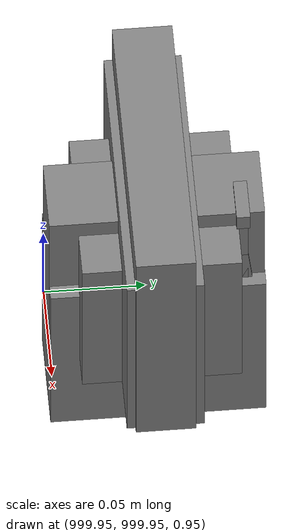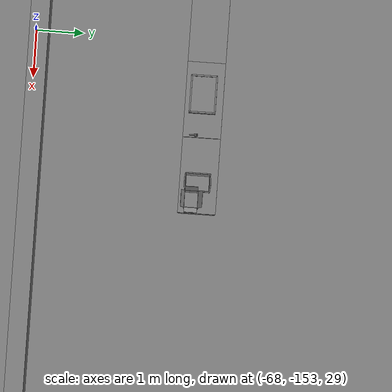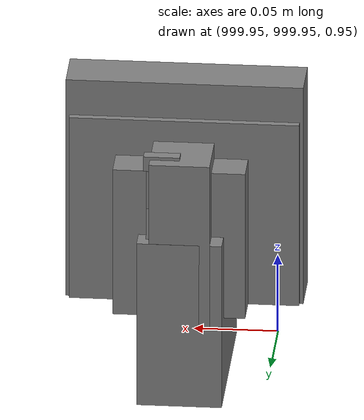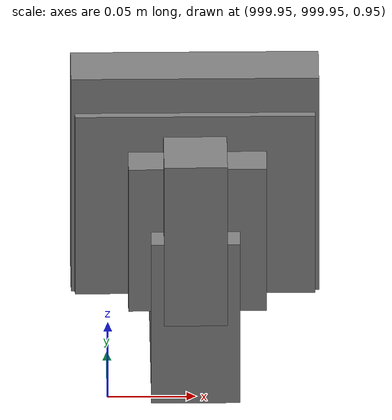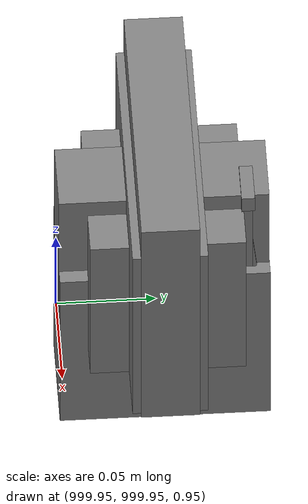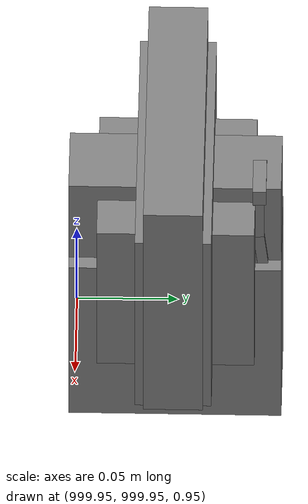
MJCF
<mujoco>
    <option gravity="0.000000000 0.000000000 -9.810000420" timestep="0.0049999999" integrator="implicitfast" density="1.225" viscosity="1.8000001e-05" noslip_iterations="10" iterations="100" sdf_iterations="50">
        <flag multiccd="disable"/>
    </option>
    <size memory="1000M"/>
    <compiler coordinate="local"/>
    <worldbody>
        <light cutoff="30" pos="0 1 1" dir="0 -1 -2"/>
        <light cutoff="30" pos="0 -1 1" dir="0 1 -2"/>
        <body pos="-64.866622925 -149.383972168 30.183746338" euler="89.999984741 89.999946594 0.000000000" name="openloong_gripper_2f85_fix_base_usda_bluebox_01">
            <geom contype="1" conaffinity="1" density="1000" type="box" material="" rgba="0.500000000 0.500000000 0.500000000 1.000000000" solimp="0.899999976 0.949999988 0.001000000" friction="1.000000000 0.005000000 0.000100000" solref="0.020000000 1.000000000" margin="0" condim="3" group="0" pos="0.276580811 0.187225342 0.000068665" quat="0.707106948 0.000077471 0.707106352 0.000077486" size="0.100000001 0.057999998 0.010000000" name="openloong_gripper_2f85_fix_base_usda_geom_33D3E1A3_E4E0_44C6_92E9_82E980D3475D"/>
            <geom contype="1" conaffinity="1" density="1000" type="box" material="" rgba="0.500000000 0.500000000 0.500000000 1.000000000" solimp="0.899999976 0.949999988 0.001000000" friction="1.000000000 0.005000000 0.000100000" solref="0.020000000 1.000000000" margin="0" condim="3" group="0" pos="0.000000000 0.002883911 0.000000000" quat="0.999999881 0.000000000 0.000000000 0.000000000" size="0.254000008 0.003000000 0.172000006" name="openloong_gripper_2f85_fix_base_usda_geom_39345D2A_C8DA_4E30_B23A_8B0639FC9CB8"/>
            <geom contype="1" conaffinity="1" density="1000" type="box" material="" rgba="0.500000000 0.500000000 0.500000000 1.000000000" solimp="0.899999976 0.949999988 0.001000000" friction="1.000000000 0.005000000 0.000100000" solref="0.020000000 1.000000000" margin="0" condim="3" group="0" pos="0.000000000 0.124874115 0.173484802" quat="0.999796331 0.020176515 -0.000000015 0.000000030" size="0.259999990 0.119999997 0.007000000" name="openloong_gripper_2f85_fix_base_usda_geom_C7173564_5CC1_4316_91BA_CD44C725E31D"/>
            <geom contype="1" conaffinity="1" density="1000" type="box" material="" rgba="0.500000000 0.500000000 0.500000000 1.000000000" solimp="0.899999976 0.949999988 0.001000000" friction="1.000000000 0.005000000 0.000100000" solref="0.020000000 1.000000000" margin="0" condim="3" group="0" pos="0.000000000 0.124874115 -0.173469543" quat="0.999796331 -0.020176545 -0.000000015 0.000000000" size="0.259999990 0.119999997 0.007000000" name="openloong_gripper_2f85_fix_base_usda_geom_3488F165_32C7_49CA_8244_1DA019350D70"/>
            <geom contype="1" conaffinity="1" density="1000" type="box" material="" rgba="0.500000000 0.500000000 0.500000000 1.000000000" solimp="0.899999976 0.949999988 0.001000000" friction="1.000000000 0.005000000 0.000100000" solref="0.020000000 1.000000000" margin="0" condim="3" group="0" pos="0.000000000 0.214008331 0.188980103" quat="0.999912977 0.013176724 0.000000015 0.000000000" size="0.259999990 0.029999999 0.012500000" name="openloong_gripper_2f85_fix_base_usda_geom_8A87ADDD_9C8C_46A9_8F56_D95945D1C0A8"/>
            <geom contype="1" conaffinity="1" density="1000" type="box" material="" rgba="0.500000000 0.500000000 0.500000000 1.000000000" solimp="0.899999976 0.949999988 0.001000000" friction="1.000000000 0.005000000 0.000100000" solref="0.020000000 1.000000000" margin="0" condim="3" group="0" pos="-0.258361816 0.125289917 0.001876831" quat="0.702796936 -0.020792112 0.710783124 0.020769298" size="0.189999998 0.119999997 0.009000000" name="openloong_gripper_2f85_fix_base_usda_geom_5207D891_DCB9_4461_AC7F_19115B305EB9"/>
            <geom contype="1" conaffinity="1" density="1000" type="box" material="" rgba="0.500000000 0.500000000 0.500000000 1.000000000" solimp="0.899999976 0.949999988 0.001000000" friction="1.000000000 0.005000000 0.000100000" solref="0.020000000 1.000000000" margin="0" condim="3" group="0" pos="0.000000000 0.214008331 -0.188980103" quat="0.999912977 -0.013176769 0.000000030 0.000000015" size="0.259999990 0.029999999 0.012500000" name="openloong_gripper_2f85_fix_base_usda_geom_77E084BF_05E2_4629_A88B_F5B48CFE1643"/>
            <geom contype="1" conaffinity="1" density="1000" type="box" material="" rgba="0.500000000 0.500000000 0.500000000 1.000000000" solimp="0.899999976 0.949999988 0.001000000" friction="1.000000000 0.005000000 0.000100000" solref="0.020000000 1.000000000" margin="0" condim="3" group="0" pos="-0.276611328 0.187225342 0.000068665" quat="0.707106650 0.000077441 0.707106709 0.000077456" size="0.100000001 0.057999998 0.010000000" name="openloong_gripper_2f85_fix_base_usda_geom_43CBABCE_C836_4DAB_BB0D_4E3FB424058D"/>
            <geom contype="1" conaffinity="1" density="1000" type="box" material="" rgba="0.500000000 0.500000000 0.500000000 1.000000000" solimp="0.899999976 0.949999988 0.001000000" friction="1.000000000 0.005000000 0.000100000" solref="0.020000000 1.000000000" margin="0" condim="3" group="0" pos="0.258331299 0.125289917 0.001876831" quat="0.702851415 0.018856421 0.710823774 -0.019329369" size="0.189999998 0.119999997 0.009000000" name="openloong_gripper_2f85_fix_base_usda_geom_93DC93AE_AE07_4689_933A_393B04349EF9"/>
            <freejoint name="openloong_gripper_2f85_fix_base_usda_bluebox_01_joint"/>
            <site size="0.005000000 0.005000000 0.005000000" rgba="0.500000000 0.500000000 0.500000000 1.000000000" pos="0.000000000 0.000000000 0.000000000" quat="0.999961913 0.008726534 0.000000000 0.000000000" group="0" type="sphere" name="openloong_gripper_2f85_fix_base_usda_bluebox_01site"/>
        </body>
        <body pos="-64.496299744 -149.491867065 30.235729218" euler="0.000000000 0.000000000 89.999946594" name="openloong_gripper_2f85_fix_base_usda_cardboardbox_01">
            <geom contype="1" conaffinity="1" density="1000" type="box" material="" rgba="0.500000000 0.500000000 0.500000000 1.000000000" solimp="0.899999976 0.949999988 0.001000000" friction="1.000000000 0.005000000 0.000100000" solref="0.020000000 1.000000000" margin="0" condim="3" group="0" pos="-0.003166199 -0.004086494 0.005052090" quat="1.000000000 0.000000000 0.000000000 0.000000000" size="0.142499998 0.177500010 0.005000000" name="openloong_gripper_2f85_fix_base_usda_geom_A91545EC_086F_4E24_86A7_528EA0E0532D"/>
            <geom contype="1" conaffinity="1" density="1000" type="box" material="" rgba="0.500000000 0.500000000 0.500000000 1.000000000" solimp="0.899999976 0.949999988 0.001000000" friction="1.000000000 0.005000000 0.000100000" solref="0.020000000 1.000000000" margin="0" condim="3" group="0" pos="-0.003166199 0.170316696 0.150570869" quat="1.000000000 0.000000000 0.000000000 0.000000000" size="0.142499998 0.005000000 0.149999991" name="openloong_gripper_2f85_fix_base_usda_geom_AE9671AC_AD6B_45A9_8DAB_B42B2E270B85"/>
            <geom contype="1" conaffinity="1" density="1000" type="box" material="" rgba="0.500000000 0.500000000 0.500000000 1.000000000" solimp="0.899999976 0.949999988 0.001000000" friction="1.000000000 0.005000000 0.000100000" solref="0.020000000 1.000000000" margin="0" condim="3" group="0" pos="-0.147399902 -0.005307198 0.150570869" quat="1.000000000 0.000000000 0.000000000 0.000000000" size="0.005000000 0.177500010 0.149999991" name="openloong_gripper_2f85_fix_base_usda_geom_DBE696BF_A373_4203_9747_0D7FABAF6821"/>
            <geom contype="1" conaffinity="1" density="1000" type="box" material="" rgba="0.500000000 0.500000000 0.500000000 1.000000000" solimp="0.899999976 0.949999988 0.001000000" friction="1.000000000 0.005000000 0.000100000" solref="0.020000000 1.000000000" margin="0" condim="3" group="0" pos="0.140275955 -0.005307198 0.150570869" quat="1.000000000 0.000000000 0.000000000 0.000000000" size="0.005000000 0.177500010 0.149999991" name="openloong_gripper_2f85_fix_base_usda_geom_D6415A18_00F0_4F0F_97E9_01B8CD31DB96"/>
            <geom contype="1" conaffinity="1" density="1000" type="box" material="" rgba="0.500000000 0.500000000 0.500000000 1.000000000" solimp="0.899999976 0.949999988 0.001000000" friction="1.000000000 0.005000000 0.000100000" solref="0.020000000 1.000000000" margin="0" condim="3" group="0" pos="-0.003166199 -0.181550980 0.150570869" quat="1.000000000 0.000000000 0.000000000 0.000000000" size="0.142499998 0.005000000 0.149999991" name="openloong_gripper_2f85_fix_base_usda_geom_C38B48E7_E826_4B7E_895F_BC550FDA2840"/>
            <freejoint name="openloong_gripper_2f85_fix_base_usda_cardboardbox_01_joint"/>
            <site size="0.005000000 0.005000000 0.005000000" rgba="0.500000000 0.500000000 0.500000000 1.000000000" pos="0.000000000 0.000000000 0.000000000" quat="0.999961913 0.008726535 0.000000000 0.000000000" group="0" type="sphere" name="openloong_gripper_2f85_fix_base_usda_site_8B05F274_2593_4454_816A_28CE3284B148"/>
            <body pos="0.139160156 -0.004048347 0.301930904" euler="-179.999954224 49.383502960 179.999954224" name="openloong_gripper_2f85_fix_base_usda_A1_006">
                <geom contype="1" conaffinity="1" density="1000" type="box" material="" rgba="0.500000000 0.500000000 0.500000000 1.000000000" solimp="0.899999976 0.949999988 0.001000000" friction="1.000000000 0.005000000 0.000100000" solref="0.020000000 1.000000000" margin="0" condim="3" group="0" pos="-0.071587563 0.000009537 0.001745224" quat="0.999999881 0.000000000 0.000000000 0.000000000" size="0.071249999 0.179999992 0.002500000" name="openloong_gripper_2f85_fix_base_usda_geom_9839ED78_4A6C_45CD_B8A9_54CCBBC421D1"/>
                <joint armature="0" stiffness="0.07" damping="0.0099999998" axis="0.000000 1.000000 0.000000" type="hinge" name="openloong_gripper_2f85_fix_base_usda_A1_006"/>
            </body>
            <body pos="-0.145902634 -0.004086494 0.301938057" euler="-180.000000000 -60.000011444 -180.000000000" name="openloong_gripper_2f85_fix_base_usda_A2_006">
                <geom contype="1" conaffinity="1" density="1000" type="box" material="" rgba="0.500000000 0.500000000 0.500000000 1.000000000" solimp="0.899999976 0.949999988 0.001000000" friction="1.000000000 0.005000000 0.000100000" solref="0.020000000 1.000000000" margin="0" condim="3" group="0" pos="0.071268082 0.000009537 0.002717972" quat="0.000002921 0.000000000 -0.000000030 0.999999881" size="0.071249999 0.179999992 0.002500000" name="openloong_gripper_2f85_fix_base_usda_geom_9F32F353_47BC_4113_AAE5_B0BA380D1725"/>
                <joint armature="0" stiffness="0.07" damping="0.0099999998" axis="0.000000 1.000000 0.000000" type="hinge" name="openloong_gripper_2f85_fix_base_usda_A2_006"/>
            </body>
            <body pos="-0.003385544 0.175991058 0.301930904" euler="-125.858116150 -0.000004561 0.000002331" name="openloong_gripper_2f85_fix_base_usda_B2_006">
                <geom contype="1" conaffinity="1" density="1000" type="box" material="" rgba="0.500000000 0.500000000 0.500000000 1.000000000" solimp="0.899999976 0.949999988 0.001000000" friction="1.000000000 0.005000000 0.000100000" solref="0.020000000 1.000000000" margin="0" condim="3" group="0" pos="0.000009537 -0.070939064 -0.002470016" quat="0.999614120 0.027776197 -0.000000015 0.000000030" size="0.137500003 0.064999998 0.005000000" name="openloong_gripper_2f85_fix_base_usda_geom_4302C06F_7077_4F64_92D3_C54923584917"/>
                <joint armature="0" stiffness="0.07" damping="0.0099999998" axis="1.000000 0.000000 0.000000" type="hinge" name="openloong_gripper_2f85_fix_base_usda_B2_006"/>
            </body>
            <body pos="-0.003385544 -0.184140205 0.301938057" euler="147.805557251 0.000000000 0.000000000" name="openloong_gripper_2f85_fix_base_usda_B1_006">
                <geom contype="1" conaffinity="1" density="1000" type="box" material="" rgba="0.500000000 0.500000000 0.500000000 1.000000000" solimp="0.899999976 0.949999988 0.001000000" friction="1.000000000 0.005000000 0.000100000" solref="0.020000000 1.000000000" margin="0" condim="3" group="0" pos="-0.000028610 0.070202351 -0.002703667" quat="0.999614179 -0.027776167 0.000000000 0.000000000" size="0.137500003 0.064999998 0.005000000" name="openloong_gripper_2f85_fix_base_usda_geom_48D71311_94B6_4143_90C2_176BEF6EDE4E"/>
                <joint armature="0" stiffness="0.07" damping="0.0099999998" axis="1.000000 0.000000 0.000000" type="hinge" name="openloong_gripper_2f85_fix_base_usda_B1_006"/>
            </body>
        </body>
        <body pos="-65.882858276 -149.481979370 30.229999542" euler="-64.487716675 0.000000000 0.000000000" name="openloong_gripper_2f85_fix_base_usda_Barcode">
            <geom contype="1" conaffinity="1" density="1000" type="box" material="" rgba="0.500000000 0.500000000 0.500000000 1.000000000" solimp="0.899999976 0.949999988 0.001000000" friction="1.000000000 0.005000000 0.000100000" solref="0.020000000 1.000000000" margin="0" condim="3" group="0" pos="0.000000000 0.013038635 0.001419067" quat="0.000000000 0.000000000 0.000000000 1.000000119" size="0.034000002 0.010000000 0.017999999" name="openloong_gripper_2f85_fix_base_usda_geom_FFF9F95C_8BD1_40B5_BB0C_43495AAF539F"/>
            <geom contype="1" conaffinity="1" density="1000" type="box" material="" rgba="0.500000000 0.500000000 0.500000000 1.000000000" solimp="0.899999976 0.949999988 0.001000000" friction="1.000000000 0.005000000 0.000100000" solref="0.020000000 1.000000000" margin="0" condim="3" group="0" pos="0.000000000 -0.035301208 -0.007095337" quat="0.000000000 0.000000000 -0.043619365 0.999048233" size="0.028999999 0.010000000 0.020000000" name="openloong_gripper_2f85_fix_base_usda_geom_D00A99C3_0A70_44DE_8588_3B911CCD43A8"/>
            <geom contype="1" conaffinity="1" density="1000" type="box" material="" rgba="0.500000000 0.500000000 0.500000000 1.000000000" solimp="0.899999976 0.949999988 0.001000000" friction="1.000000000 0.005000000 0.000100000" solref="0.020000000 1.000000000" margin="0" condim="3" group="0" pos="0.000000000 -0.043411255 -0.011749268" quat="0.922262907 0.386563420 0.000000000 0.000000000" size="0.026000001 0.010000000 0.020000000" name="openloong_gripper_2f85_fix_base_usda_geom_8A63FC1B_8C22_4955_8D0A_54F8A7FC52B7"/>
            <geom contype="1" conaffinity="1" density="1000" type="box" material="" rgba="0.500000000 0.500000000 0.500000000 1.000000000" solimp="0.899999976 0.949999988 0.001000000" friction="1.000000000 0.005000000 0.000100000" solref="0.020000000 1.000000000" margin="0" condim="3" group="0" pos="0.000000000 -0.016967773 -0.031860352" quat="0.000000000 0.000000000 0.000000000 1.000000119" size="0.008000000 0.010000000 0.013000000" name="openloong_gripper_2f85_fix_base_usda_geom_D72BD4FF_EF76_4B57_BD4A_506D3F3D82E9"/>
            <geom contype="1" conaffinity="1" density="1000" type="box" material="" rgba="0.500000000 0.500000000 0.500000000 1.000000000" solimp="0.899999976 0.949999988 0.001000000" friction="1.000000000 0.005000000 0.000100000" solref="0.020000000 1.000000000" margin="0" condim="3" group="0" pos="0.000000000 -0.001869202 0.000312805" quat="0.953716993 0.300705761 0.000000000 0.000000000" size="0.032000002 0.010000000 0.018999999" name="openloong_gripper_2f85_fix_base_usda_geom_8C658A88_9773_4DF5_860A_2166C1A3C3A5"/>
            <geom contype="1" conaffinity="1" density="1000" type="box" material="" rgba="0.500000000 0.500000000 0.500000000 1.000000000" solimp="0.899999976 0.949999988 0.001000000" friction="1.000000000 0.005000000 0.000100000" solref="0.020000000 1.000000000" margin="0" condim="3" group="0" pos="0.000000000 -0.019531250 -0.003173828" quat="0.953716993 0.300705761 0.000000000 0.000000000" size="0.030999999 0.010000000 0.020000000" name="openloong_gripper_2f85_fix_base_usda_geom_91C8A72B_320C_4DE9_884F_25B305C6F322"/>
            <geom contype="1" conaffinity="1" density="1000" type="box" material="" rgba="0.500000000 0.500000000 0.500000000 1.000000000" solimp="0.899999976 0.949999988 0.001000000" friction="1.000000000 0.005000000 0.000100000" solref="0.020000000 1.000000000" margin="0" condim="3" group="0" pos="0.000000000 -0.035301208 -0.007095337" quat="0.953716993 0.300705761 0.000000000 0.000000000" size="0.028999999 0.010000000 0.020000000" name="openloong_gripper_2f85_fix_base_usda_geom_19AC9EAA_77E0_4AC3_9407_B61B9A04ADFC"/>
            <geom contype="1" conaffinity="1" density="1000" type="box" material="" rgba="0.500000000 0.500000000 0.500000000 1.000000000" solimp="0.899999976 0.949999988 0.001000000" friction="1.000000000 0.005000000 0.000100000" solref="0.020000000 1.000000000" margin="0" condim="3" group="0" pos="0.000000000 -0.042617798 -0.071121216" quat="0.000000000 0.000000000 0.000000000 1.000000119" size="0.013000000 0.021000000 0.059999999" name="openloong_gripper_2f85_fix_base_usda_geom_5F557399_34EA_4040_BB2F_21C49866671D"/>
            <freejoint name="openloong_gripper_2f85_fix_base_usda_Barcode_joint"/>
            <site size="0.005000000 0.005000000 0.005000000" rgba="0.500000000 0.500000000 0.500000000 1.000000000" pos="0.000000000 0.000000000 0.000000000" quat="1.000000000 0.000000000 0.000000000 0.000000000" group="0" type="sphere" name="openloong_gripper_2f85_fix_base_usda_Barcode_site"/>
        </body>
        <body pos="-66.745018005 -149.392349243 30.184000015" euler="0.000000000 0.000000000 89.999946594" name="[22332028647469]_Basket_01">
            <geom contype="1" conaffinity="1" density="1000" type="box" material="" rgba="0.500000000 0.500000000 0.500000000 1.000000000" solimp="0.899999976 0.949999988 0.001000000" friction="1.000000000 0.005000000 0.000100000" solref="0.020000000 1.000000000" margin="0" condim="3" group="0" pos="-0.052425385 0.389207840 0.089787483" quat="0.707107008 0.000000000 0.000000000 0.707106411" size="0.014249999 0.014249999 0.059999999" name="[22332028647469]_geom_0FFACCE4_5423_432C_944C_3DCC03DE2E8E"/>
            <geom contype="1" conaffinity="1" density="1000" type="box" material="" rgba="0.500000000 0.500000000 0.500000000 1.000000000" solimp="0.899999976 0.949999988 0.001000000" friction="1.000000000 0.005000000 0.000100000" solref="0.020000000 1.000000000" margin="0" condim="3" group="0" pos="0.264015198 -0.133043289 0.089787483" quat="0.707107008 0.000000000 0.000000000 0.707106411" size="0.014249999 0.014249999 0.059999999" name="[22332028647469]_geom_C0EF316C_BBC2_4AE6_8F6A_5ECB4B9F8735"/>
            <geom contype="1" conaffinity="1" density="1000" type="box" material="" rgba="0.500000000 0.500000000 0.500000000 1.000000000" solimp="0.899999976 0.949999988 0.001000000" friction="1.000000000 0.005000000 0.000100000" solref="0.020000000 1.000000000" margin="0" condim="3" group="0" pos="-0.264015198 -0.265548706 0.089793205" quat="0.707107008 0.000000000 0.000000000 0.707106411" size="0.014249999 0.014249999 0.059999999" name="[22332028647469]_geom_ED78E17D_6096_49A5_97DD_D26351A43384"/>
            <geom contype="1" conaffinity="1" density="1000" type="box" material="" rgba="0.500000000 0.500000000 0.500000000 1.000000000" solimp="0.899999976 0.949999988 0.001000000" friction="1.000000000 0.005000000 0.000100000" solref="0.020000000 1.000000000" margin="0" condim="3" group="0" pos="-0.160263062 -0.389322281 0.089793205" quat="0.707107008 0.000000000 0.000000000 0.707106411" size="0.014249999 0.014249999 0.059999999" name="[22332028647469]_geom_BAED566C_0F1D_43AA_BE57_8DB9EA2748DB"/>
            <geom contype="1" conaffinity="1" density="1000" type="box" material="" rgba="0.500000000 0.500000000 0.500000000 1.000000000" solimp="0.899999976 0.949999988 0.001000000" friction="1.000000000 0.005000000 0.000100000" solref="0.020000000 1.000000000" margin="0" condim="3" group="0" pos="0.162265778 -0.389322281 0.089787483" quat="0.707107008 0.000000000 0.000000000 0.707106411" size="0.014249999 0.014249999 0.059999999" name="[22332028647469]_geom_7F813E4E_A3AC_4417_AACD_E6B9FBD592B5"/>
            <geom contype="1" conaffinity="1" density="1000" type="box" material="" rgba="0.500000000 0.500000000 0.500000000 1.000000000" solimp="0.899999976 0.949999988 0.001000000" friction="1.000000000 0.005000000 0.000100000" solref="0.020000000 1.000000000" margin="0" condim="3" group="0" pos="0.264015198 0.389207840 0.089787483" quat="0.707107008 0.000000000 0.000000000 0.707106411" size="0.014249999 0.014249999 0.059999999" name="[22332028647469]_geom_373E868F_14EA_467E_8D9E_BF68CFAC024C"/>
            <geom contype="1" conaffinity="1" density="1000" type="box" material="" rgba="0.500000000 0.500000000 0.500000000 1.000000000" solimp="0.899999976 0.949999988 0.001000000" friction="1.000000000 0.005000000 0.000100000" solref="0.020000000 1.000000000" margin="0" condim="3" group="0" pos="-0.264015198 -0.133043289 0.089793205" quat="0.707107008 0.000000000 0.000000000 0.707106411" size="0.014249999 0.014249999 0.059999999" name="[22332028647469]_geom_FB4D56D1_BD04_4D61_9AEB_8731FBFF1463"/>
            <geom contype="1" conaffinity="1" density="1000" type="box" material="" rgba="0.500000000 0.500000000 0.500000000 1.000000000" solimp="0.899999976 0.949999988 0.001000000" friction="1.000000000 0.005000000 0.000100000" solref="0.020000000 1.000000000" margin="0" condim="3" group="0" pos="-0.264026642 0.269256592 0.089793205" quat="0.707107008 0.000000000 0.000000000 0.707106411" size="0.014249999 0.014249999 0.059999999" name="[22332028647469]_geom_048E48B0_6121_4CDC_B89C_1A4532674C24"/>
            <geom contype="1" conaffinity="1" density="1000" type="box" material="" rgba="0.500000000 0.500000000 0.500000000 1.000000000" solimp="0.899999976 0.949999988 0.001000000" friction="1.000000000 0.005000000 0.000100000" solref="0.020000000 1.000000000" margin="0" condim="3" group="0" pos="0.054462433 0.389207840 0.089787483" quat="0.707107008 0.000000000 0.000000000 0.707106411" size="0.014249999 0.014249999 0.059999999" name="[22332028647469]_geom_D5EC4527_755F_457B_8AAE_80E976AF6B86"/>
            <geom contype="1" conaffinity="1" density="1000" type="box" material="" rgba="0.500000000 0.500000000 0.500000000 1.000000000" solimp="0.899999976 0.949999988 0.001000000" friction="1.000000000 0.005000000 0.000100000" solref="0.020000000 1.000000000" margin="0" condim="3" group="0" pos="0.054462433 -0.389322281 0.089787483" quat="0.707107008 0.000000000 0.000000000 0.707106411" size="0.014249999 0.014249999 0.059999999" name="[22332028647469]_geom_D9248FFE_527D_412F_B29D_A95DDF995EA7"/>
            <geom contype="1" conaffinity="1" density="1000" type="box" material="" rgba="0.500000000 0.500000000 0.500000000 1.000000000" solimp="0.899999976 0.949999988 0.001000000" friction="1.000000000 0.005000000 0.000100000" solref="0.020000000 1.000000000" margin="0" condim="3" group="0" pos="0.264015198 0.269256592 0.089793205" quat="0.707107008 0.000000000 0.000000000 0.707106411" size="0.014249999 0.014249999 0.059999999" name="[22332028647469]_geom_71E25EBE_5FE1_4CDF_9D02_6C18E44B8FB5"/>
            <geom contype="1" conaffinity="1" density="1000" type="box" material="" rgba="0.500000000 0.500000000 0.500000000 1.000000000" solimp="0.899999976 0.949999988 0.001000000" friction="1.000000000 0.005000000 0.000100000" solref="0.020000000 1.000000000" margin="0" condim="3" group="0" pos="0.264015198 -0.389322281 0.089787483" quat="0.707107008 0.000000000 0.000000000 0.707106411" size="0.014249999 0.014249999 0.059999999" name="[22332028647469]_geom_85461C58_F7C0_40A2_84DE_3EFF372968AB"/>
            <geom contype="1" conaffinity="1" density="1000" type="box" material="" rgba="0.500000000 0.500000000 0.500000000 1.000000000" solimp="0.899999976 0.949999988 0.001000000" friction="1.000000000 0.005000000 0.000100000" solref="0.020000000 1.000000000" margin="0" condim="3" group="0" pos="0.000000000 0.000000000 0.015998840" quat="0.707107008 0.000000000 0.000000000 0.707106411" size="0.403499991 0.279000014 0.015750000" name="[22332028647469]_geom_CD0922A9_A126_4F94_9722_5282E72AD9F4"/>
            <geom contype="1" conaffinity="1" density="1000" type="box" material="" rgba="0.500000000 0.500000000 0.500000000 1.000000000" solimp="0.899999976 0.949999988 0.001000000" friction="1.000000000 0.005000000 0.000100000" solref="0.020000000 1.000000000" margin="0" condim="3" group="0" pos="0.000000000 -0.389476776 0.163619041" quat="0.707107008 0.000000000 0.000000000 0.707106411" size="0.015000000 0.277500004 0.015750000" name="[22332028647469]_geom_39209CE4_A4E8_4927_9204_AF4B587421C1"/>
            <geom contype="1" conaffinity="1" density="1000" type="box" material="" rgba="0.500000000 0.500000000 0.500000000 1.000000000" solimp="0.899999976 0.949999988 0.001000000" friction="1.000000000 0.005000000 0.000100000" solref="0.020000000 1.000000000" margin="0" condim="3" group="0" pos="0.162265778 0.389207840 0.089787483" quat="0.707107008 0.000000000 0.000000000 0.707106411" size="0.014249999 0.014249999 0.059999999" name="[22332028647469]_geom_96C8B0B2_F2DE_44EF_900D_46CB3072C6AE"/>
            <geom contype="1" conaffinity="1" density="1000" type="box" material="" rgba="0.500000000 0.500000000 0.500000000 1.000000000" solimp="0.899999976 0.949999988 0.001000000" friction="1.000000000 0.005000000 0.000100000" solref="0.020000000 1.000000000" margin="0" condim="3" group="0" pos="0.000000000 0.389471054 0.163619041" quat="0.707107008 0.000000000 0.000000000 0.707106411" size="0.015000000 0.277500004 0.015750000" name="[22332028647469]_geom_55754636_36AF_4AF0_B97D_1D8FC1094FBF"/>
            <geom contype="1" conaffinity="1" density="1000" type="box" material="" rgba="0.500000000 0.500000000 0.500000000 1.000000000" solimp="0.899999976 0.949999988 0.001000000" friction="1.000000000 0.005000000 0.000100000" solref="0.020000000 1.000000000" margin="0" condim="3" group="0" pos="-0.263511658 0.000000000 0.163619041" quat="0.707107008 0.000000000 0.000000000 0.707106411" size="0.403499991 0.015000000 0.015750000" name="[22332028647469]_geom_11F7F755_B568_42B2_935D_2F8212199790"/>
            <geom contype="1" conaffinity="1" density="1000" type="box" material="" rgba="0.500000000 0.500000000 0.500000000 1.000000000" solimp="0.899999976 0.949999988 0.001000000" friction="1.000000000 0.005000000 0.000100000" solref="0.020000000 1.000000000" margin="0" condim="3" group="0" pos="-0.264015198 0.141334534 0.089793205" quat="0.707107008 0.000000000 0.000000000 0.707106411" size="0.014249999 0.014249999 0.059999999" name="[22332028647469]_geom_46213C11_9A6E_4238_9D79_B986FBB7BFB3"/>
            <geom contype="1" conaffinity="1" density="1000" type="box" material="" rgba="0.500000000 0.500000000 0.500000000 1.000000000" solimp="0.899999976 0.949999988 0.001000000" friction="1.000000000 0.005000000 0.000100000" solref="0.020000000 1.000000000" margin="0" condim="3" group="0" pos="0.264015198 -0.265548706 0.089787483" quat="0.707107008 0.000000000 0.000000000 0.707106411" size="0.014249999 0.014249999 0.059999999" name="[22332028647469]_geom_41DC7F3A_4C6D_46C1_A66C_3692A93BE9CA"/>
            <geom contype="1" conaffinity="1" density="1000" type="box" material="" rgba="0.500000000 0.500000000 0.500000000 1.000000000" solimp="0.899999976 0.949999988 0.001000000" friction="1.000000000 0.005000000 0.000100000" solref="0.020000000 1.000000000" margin="0" condim="3" group="0" pos="-0.160263062 0.389207840 0.089787483" quat="0.707107008 0.000000000 0.000000000 0.707106411" size="0.014249999 0.014249999 0.059999999" name="[22332028647469]_geom_E98EED43_09FB_4638_9D12_448D5A6E0BA1"/>
            <geom contype="1" conaffinity="1" density="1000" type="box" material="" rgba="0.500000000 0.500000000 0.500000000 1.000000000" solimp="0.899999976 0.949999988 0.001000000" friction="1.000000000 0.005000000 0.000100000" solref="0.020000000 1.000000000" margin="0" condim="3" group="0" pos="-0.052425385 -0.389322281 0.089787483" quat="0.707107008 0.000000000 0.000000000 0.707106411" size="0.014249999 0.014249999 0.059999999" name="[22332028647469]_geom_4019EFE9_17C0_4D34_97F3_4EBB0A06C00D"/>
            <geom contype="1" conaffinity="1" density="1000" type="box" material="" rgba="0.500000000 0.500000000 0.500000000 1.000000000" solimp="0.899999976 0.949999988 0.001000000" friction="1.000000000 0.005000000 0.000100000" solref="0.020000000 1.000000000" margin="0" condim="3" group="0" pos="-0.264026642 -0.389322281 0.089793205" quat="0.707107008 0.000000000 0.000000000 0.707106411" size="0.014249999 0.014249999 0.059999999" name="[22332028647469]_geom_C096E59B_9EDC_4D41_853D_4C8488D71244"/>
            <geom contype="1" conaffinity="1" density="1000" type="box" material="" rgba="0.500000000 0.500000000 0.500000000 1.000000000" solimp="0.899999976 0.949999988 0.001000000" friction="1.000000000 0.005000000 0.000100000" solref="0.020000000 1.000000000" margin="0" condim="3" group="0" pos="0.264015198 0.141334534 0.089787483" quat="0.707107008 0.000000000 0.000000000 0.707106411" size="0.014249999 0.014249999 0.059999999" name="[22332028647469]_geom_63B8BC73_4068_441F_A8DE_C6437F50F444"/>
            <geom contype="1" conaffinity="1" density="1000" type="box" material="" rgba="0.500000000 0.500000000 0.500000000 1.000000000" solimp="0.899999976 0.949999988 0.001000000" friction="1.000000000 0.005000000 0.000100000" solref="0.020000000 1.000000000" margin="0" condim="3" group="0" pos="-0.264015198 0.389207840 0.089793205" quat="0.707107008 0.000000000 0.000000000 0.707106411" size="0.014249999 0.014249999 0.059999999" name="[22332028647469]_geom_346A80B5_96A5_4E0F_B0E0_3302657EBD2A"/>
            <geom contype="1" conaffinity="1" density="1000" type="box" material="" rgba="0.500000000 0.500000000 0.500000000 1.000000000" solimp="0.899999976 0.949999988 0.001000000" friction="1.000000000 0.005000000 0.000100000" solref="0.020000000 1.000000000" margin="0" condim="3" group="0" pos="0.264015198 0.004480362 0.089787483" quat="0.707107008 0.000000000 0.000000000 0.707106411" size="0.014249999 0.014249999 0.059999999" name="[22332028647469]_geom_91E52AD2_B5CF_495D_B8A1_15906E338B5D"/>
            <geom contype="1" conaffinity="1" density="1000" type="box" material="" rgba="0.500000000 0.500000000 0.500000000 1.000000000" solimp="0.899999976 0.949999988 0.001000000" friction="1.000000000 0.005000000 0.000100000" solref="0.020000000 1.000000000" margin="0" condim="3" group="0" pos="0.263694763 -0.000011444 0.163619041" quat="0.707107008 0.000000000 0.000000000 0.707106411" size="0.403499991 0.015000000 0.015750000" name="[22332028647469]_geom_6DB555D3_CFCD_4CAB_8B58_4D22DF18D9BD"/>
            <geom contype="1" conaffinity="1" density="1000" type="box" material="" rgba="0.500000000 0.500000000 0.500000000 1.000000000" solimp="0.899999976 0.949999988 0.001000000" friction="1.000000000 0.005000000 0.000100000" solref="0.020000000 1.000000000" margin="0" condim="3" group="0" pos="-0.264015198 0.004480362 0.089793205" quat="0.707107008 0.000000000 0.000000000 0.707106411" size="0.014249999 0.014249999 0.059999999" name="[22332028647469]_geom_F6F2192F_F57D_4635_9B78_6531E4EB8467"/>
            <freejoint name="[22332028647469]_joint_1B3A8114_D710_4700_BAAE_313C7759AEBA"/>
        </body>
        <body pos="0.000000000 0.000000000 0.000000000" euler="0.000000000 0.000000000 0.000000000" name="Static Objects_Static Objects">
            <geom contype="1" conaffinity="1" density="1000" type="box" material="" rgba="0.500000000 0.500000000 0.500000000 1.000000000" solimp="0.899999976 0.949999988 0.001000000" friction="1.000000000 0.005000000 0.000100000" solref="0.020000000 1.000000000" margin="0" condim="3" group="0" pos="-67.544113159 -149.365814209 29.727830887" quat="0.500000417 0.499999970 0.499999553 0.499999970" size="0.381000012 0.319999993 0.041000001" name="Static Objects_geom_DA57A85F_E22C_420F_B396_7554A47FB442"/>
            <geom contype="1" conaffinity="1" density="1000" type="box" material="" rgba="0.500000000 0.500000000 0.500000000 1.000000000" solimp="0.899999976 0.949999988 0.001000000" friction="1.000000000 0.005000000 0.000100000" solref="0.020000000 1.000000000" margin="0" condim="3" group="0" pos="-68.239501953 -149.365814209 30.086868286" quat="0.500000417 0.499999970 0.499999553 0.499999970" size="0.370999992 0.039500002 0.745000005" name="Static Objects_geom_94507ADD_F8C2_41E2_AD9E_1A6C3341209B"/>
            <geom contype="1" conaffinity="1" density="1000" type="box" material="" rgba="0.500000000 0.500000000 0.500000000 1.000000000" solimp="0.899999976 0.949999988 0.001000000" friction="1.000000000 0.005000000 0.000100000" solref="0.020000000 1.000000000" margin="0" condim="3" group="0" pos="-68.239501953 -149.365814209 30.147235870" quat="0.500000417 0.499999970 0.499999553 0.499999970" size="0.400000006 0.022000000 0.800000012" name="Static Objects_geom_6B6D3EB5_0C45_45A5_8992_1393A6CA8982"/>
            <geom contype="1" conaffinity="1" density="1000" type="box" material="" rgba="0.500000000 0.500000000 0.500000000 1.000000000" solimp="0.899999976 0.949999988 0.001000000" friction="1.000000000 0.005000000 0.000100000" solref="0.020000000 1.000000000" margin="0" condim="3" group="0" pos="-68.934890747 -149.365814209 29.727830887" quat="0.500000417 0.499999970 0.499999553 0.499999970" size="0.381000012 0.319999993 0.041000001" name="Static Objects_geom_1FAB0DEC_4E90_4A85_8370_C6FBCFC96E63"/>
            <geom contype="1" conaffinity="1" density="1000" type="box" material="" rgba="0.500000000 0.500000000 0.500000000 1.000000000" solimp="0.899999976 0.949999988 0.001000000" friction="1.000000000 0.005000000 0.000100000" solref="0.020000000 1.000000000" margin="0" condim="3" group="0" pos="-68.239501953 -149.365814209 29.561563492" quat="0.500000417 0.499999970 0.499999553 0.499999970" size="0.020000000 0.022000000 0.660000026" name="Static Objects_geom_2EF1AF33_BE21_4503_9412_F48F9BA0B60A"/>
            <geom contype="1" conaffinity="1" density="1000" type="box" material="" rgba="0.500000000 0.500000000 0.500000000 1.000000000" solimp="0.899999976 0.949999988 0.001000000" friction="1.000000000 0.005000000 0.000100000" solref="0.020000000 1.000000000" margin="0" condim="3" group="0" pos="-65.945671082 -149.365814209 29.727830887" quat="0.500000417 0.499999970 0.499999553 0.499999970" size="0.381000012 0.319999993 0.041000001" name="Static Objects_geom_B95DAD45_96D7_4E37_8525_0985D38D69AD"/>
            <geom contype="1" conaffinity="1" density="1000" type="box" material="" rgba="0.500000000 0.500000000 0.500000000 1.000000000" solimp="0.899999976 0.949999988 0.001000000" friction="1.000000000 0.005000000 0.000100000" solref="0.020000000 1.000000000" margin="0" condim="3" group="0" pos="-66.641059875 -149.365814209 30.086868286" quat="0.500000417 0.499999970 0.499999553 0.499999970" size="0.370999992 0.039500002 0.745000005" name="Static Objects_geom_F7C35221_5D70_4771_8A13_4AAE4532A9FD"/>
            <geom contype="1" conaffinity="1" density="1000" type="box" material="" rgba="0.500000000 0.500000000 0.500000000 1.000000000" solimp="0.899999976 0.949999988 0.001000000" friction="1.000000000 0.005000000 0.000100000" solref="0.020000000 1.000000000" margin="0" condim="3" group="0" pos="-66.641059875 -149.365814209 30.147235870" quat="0.500000417 0.499999970 0.499999553 0.499999970" size="0.400000006 0.022000000 0.800000012" name="Static Objects_geom_24A22A61_8713_4CAF_A98E_E4EC44CA6592"/>
            <geom contype="1" conaffinity="1" density="1000" type="box" material="" rgba="0.500000000 0.500000000 0.500000000 1.000000000" solimp="0.899999976 0.949999988 0.001000000" friction="1.000000000 0.005000000 0.000100000" solref="0.020000000 1.000000000" margin="0" condim="3" group="0" pos="-67.336448669 -149.365814209 29.727830887" quat="0.500000417 0.499999970 0.499999553 0.499999970" size="0.381000012 0.319999993 0.041000001" name="Static Objects_geom_3EA19346_367E_49C2_872F_7C3CACBD8F80"/>
            <geom contype="1" conaffinity="1" density="1000" type="box" material="" rgba="0.500000000 0.500000000 0.500000000 1.000000000" solimp="0.899999976 0.949999988 0.001000000" friction="1.000000000 0.005000000 0.000100000" solref="0.020000000 1.000000000" margin="0" condim="3" group="0" pos="-66.641059875 -149.365814209 29.561563492" quat="0.500000417 0.499999970 0.499999553 0.499999970" size="0.020000000 0.022000000 0.660000026" name="Static Objects_geom_D406C713_BCD3_41AC_AA94_E54FECFA73B3"/>
            <geom contype="1" conaffinity="1" density="1000" type="box" material="" rgba="0.500000000 0.500000000 0.500000000 1.000000000" solimp="0.899999976 0.949999988 0.001000000" friction="1.000000000 0.005000000 0.000100000" solref="0.020000000 1.000000000" margin="0" condim="3" group="0" pos="-64.338577271 -149.365814209 29.727830887" quat="0.500000417 0.499999970 0.499999553 0.499999970" size="0.381000012 0.319999993 0.041000001" name="Static Objects_geom_5B25525D_D49B_4A57_B51B_76F90E570832"/>
            <geom contype="1" conaffinity="1" density="1000" type="box" material="" rgba="0.500000000 0.500000000 0.500000000 1.000000000" solimp="0.899999976 0.949999988 0.001000000" friction="1.000000000 0.005000000 0.000100000" solref="0.020000000 1.000000000" margin="0" condim="3" group="0" pos="-65.033966064 -149.365814209 30.086868286" quat="0.500000417 0.499999970 0.499999553 0.499999970" size="0.370999992 0.039500002 0.745000005" name="Static Objects_geom_CD95298C_1B76_4067_A668_AA085E5028CE"/>
            <geom contype="1" conaffinity="1" density="1000" type="box" material="" rgba="0.500000000 0.500000000 0.500000000 1.000000000" solimp="0.899999976 0.949999988 0.001000000" friction="1.000000000 0.005000000 0.000100000" solref="0.020000000 1.000000000" margin="0" condim="3" group="0" pos="-65.033966064 -149.365814209 30.147235870" quat="0.500000417 0.499999970 0.499999553 0.499999970" size="0.400000006 0.022000000 0.800000012" name="Static Objects_geom_A4FDF15C_DF00_44A8_953D_203C4350DD29"/>
            <geom contype="1" conaffinity="1" density="1000" type="box" material="" rgba="0.500000000 0.500000000 0.500000000 1.000000000" solimp="0.899999976 0.949999988 0.001000000" friction="1.000000000 0.005000000 0.000100000" solref="0.020000000 1.000000000" margin="0" condim="3" group="0" pos="-65.729354858 -149.365814209 29.727830887" quat="0.500000417 0.499999970 0.499999553 0.499999970" size="0.381000012 0.319999993 0.041000001" name="Static Objects_geom_298A3FEA_86C3_49C7_991F_34120CD0A50E"/>
            <geom contype="1" conaffinity="1" density="1000" type="box" material="" rgba="0.500000000 0.500000000 0.500000000 1.000000000" solimp="0.899999976 0.949999988 0.001000000" friction="1.000000000 0.005000000 0.000100000" solref="0.020000000 1.000000000" margin="0" condim="3" group="0" pos="-65.033966064 -149.365814209 29.561563492" quat="0.500000417 0.499999970 0.499999553 0.499999970" size="0.020000000 0.022000000 0.660000026" name="Static Objects_geom_2A1D4771_7F95_4F1B_BA9B_418CBF4941FD"/>
            <geom contype="1" conaffinity="1" density="1000" type="box" material="" rgba="0.500000000 0.500000000 0.500000000 1.000000000" solimp="0.899999976 0.949999988 0.001000000" friction="1.000000000 0.005000000 0.000100000" solref="0.020000000 1.000000000" margin="0" condim="3" group="0" pos="-61.754566193 -137.853729248 33.906845093" quat="0.707107067 0.000000000 0.000000000 0.707106471" size="0.759999990 0.759999990 4.500000000" name="Static Objects_geom_6B6588F1_7823_47E4_9903_85560AD00AF0"/>
            <geom contype="1" conaffinity="1" density="1000" type="box" material="" rgba="0.500000000 0.500000000 0.500000000 1.000000000" solimp="0.899999976 0.949999988 0.001000000" friction="1.000000000 0.005000000 0.000100000" solref="0.020000000 1.000000000" margin="0" condim="3" group="0" pos="-57.511135101 -144.927108765 31.707921982" quat="1.000000000 0.000000000 0.000000000 0.000000000" size="0.200000003 8.000000000 2.299999952" name="Static Objects_geom_C217EC1C_E603_4396_8170_256FF4A7059D"/>
            <geom contype="1" conaffinity="1" density="1000" type="box" material="" rgba="0.500000000 0.500000000 0.500000000 1.000000000" solimp="0.899999976 0.949999988 0.001000000" friction="1.000000000 0.005000000 0.000100000" solref="0.020000000 1.000000000" margin="0" condim="3" group="0" pos="-80.517646790 -157.574050903 31.688196182" quat="0.707107067 0.000000000 0.000000000 0.707106471" size="0.600000024 0.600000024 2.299999952" name="Static Objects_geom_F3D59A80_CC81_43F8_A400_7F13049620CE"/>
            <geom contype="1" conaffinity="1" density="1000" type="box" material="" rgba="0.500000000 0.500000000 0.500000000 1.000000000" solimp="0.899999976 0.949999988 0.001000000" friction="1.000000000 0.005000000 0.000100000" solref="0.020000000 1.000000000" margin="0" condim="3" group="0" pos="-80.711044312 -147.414932251 31.666158676" quat="1.000000000 0.000000000 0.000000000 0.000000000" size="0.200000003 10.000000000 2.299999952" name="Static Objects_geom_2E24AB74_CD86_4D71_B603_9F47EBD51016"/>
            <geom contype="1" conaffinity="1" density="1000" type="box" material="" rgba="0.500000000 0.500000000 0.500000000 1.000000000" solimp="0.899999976 0.949999988 0.001000000" friction="1.000000000 0.005000000 0.000100000" solref="0.020000000 1.000000000" margin="0" condim="3" group="0" pos="-57.687217712 -137.434692383 31.688196182" quat="0.707107067 0.000000000 0.000000000 0.707106471" size="0.600000024 0.600000024 2.299999952" name="Static Objects_geom_6B08DE4F_1DC0_4C61_BB8D_072C4332697A"/>
            <geom contype="1" conaffinity="1" density="1000" type="box" material="" rgba="0.500000000 0.500000000 0.500000000 1.000000000" solimp="0.899999976 0.949999988 0.001000000" friction="1.000000000 0.005000000 0.000100000" solref="0.020000000 1.000000000" margin="0" condim="3" group="0" pos="-69.537033081 -140.263229370 31.714921951" quat="0.707107067 0.000000000 0.000000000 0.707106471" size="0.759999990 4.500000000 2.299999952" name="Static Objects_geom_5B24FF71_1E3A_42D4_A7CA_F6219D28CE1B"/>
            <geom contype="1" conaffinity="1" density="1000" type="box" material="" rgba="0.500000000 0.500000000 0.500000000 1.000000000" solimp="0.899999976 0.949999988 0.001000000" friction="1.000000000 0.005000000 0.000100000" solref="0.020000000 1.000000000" margin="0" condim="3" group="0" pos="-80.073638916 -137.853713989 33.906845093" quat="0.707107067 0.000000000 0.000000000 0.707106471" size="0.759999990 0.759999990 4.500000000" name="Static Objects_geom_724E9074_EA30_4098_9411_8826BF6CB8F7"/>
            <geom contype="1" conaffinity="1" density="1000" type="box" material="" rgba="0.500000000 0.500000000 0.500000000 1.000000000" solimp="0.899999976 0.949999988 0.001000000" friction="1.000000000 0.005000000 0.000100000" solref="0.020000000 1.000000000" margin="0" condim="3" group="0" pos="-73.406707764 -155.734664917 31.707921982" quat="1.000000000 0.000000000 0.000000000 0.000000000" size="0.200000003 3.000000000 2.299999952" name="Static Objects_geom_E5802192_BA6F_4ABD_8613_58CBAB1E552E"/>
            <geom contype="1" conaffinity="1" density="1000" type="box" material="" rgba="0.500000000 0.500000000 0.500000000 1.000000000" solimp="0.899999976 0.949999988 0.001000000" friction="1.000000000 0.005000000 0.000100000" solref="0.020000000 1.000000000" margin="0" condim="3" group="0" pos="-68.497543335 -137.448257446 31.707921982" quat="0.707107067 0.000000000 0.000000000 0.707106471" size="0.200000003 14.000000000 2.299999952" name="Static Objects_geom_82623624_899E_48D4_B7EF_8DC2AD99744A"/>
            <geom contype="1" conaffinity="1" density="1000" type="cylinder" material="" rgba="0.500000000 0.500000000 0.500000000 1.000000000" solimp="0.899999976 0.949999988 0.001000000" friction="1.000000000 0.005000000 0.000100000" solref="0.020000000 1.000000000" margin="0" condim="3" group="0" pos="-68.868522644 -142.134506226 31.711090088" quat="0.707107067 0.000000000 0.000000000 0.707106471" size="0.509999990 2.299999952 1.000000000" name="Static Objects_geom_FF94AE05_2B86_41FB_80E3_B23B8C30FBA3"/>
            <geom contype="1" conaffinity="1" density="1000" type="plane" material="" rgba="0.500000000 0.500000000 0.500000000 1.000000000" solimp="0.899999976 0.949999988 0.001000000" friction="1.000000000 0.005000000 0.000100000" solref="0.020000000 1.000000000" margin="0" condim="3" group="0" pos="-72.873703003 -147.131927490 29.409669876" quat="1.000000000 0.000000000 0.000000000 0.000000000" size="18.000000000 14.000000000 1.000000000" name="Static Objects_geom_1FDB41EA_E110_4003_AF0D_2EA020FCF189"/>
            <geom contype="1" conaffinity="1" density="1000" type="box" material="" rgba="0.500000000 0.500000000 0.500000000 1.000000000" solimp="0.899999976 0.949999988 0.001000000" friction="1.000000000 0.005000000 0.000100000" solref="0.020000000 1.000000000" margin="0" condim="3" group="0" pos="-79.943580627 -157.782272339 31.707921982" quat="0.707107067 0.000000000 0.000000000 0.707106471" size="0.200000003 7.000000000 2.299999952" name="Static Objects_geom_C2223765_5528_4215_9DF8_65F2077234F1"/>
            <geom contype="1" conaffinity="1" density="1000" type="box" material="" rgba="0.500000000 0.500000000 0.500000000 1.000000000" solimp="0.899999976 0.949999988 0.001000000" friction="1.000000000 0.005000000 0.000100000" solref="0.020000000 1.000000000" margin="0" condim="3" group="0" pos="-65.421028137 -152.903442383 31.707921982" quat="0.707107067 0.000000000 0.000000000 0.707106471" size="0.200000003 7.800000191 2.299999952" name="Static Objects_geom_F2CC0518_AA9B_40C0_B92C_1C33383CCC6C"/>
            <geom contype="1" conaffinity="1" density="1000" type="box" material="" rgba="0.500000000 0.500000000 0.500000000 1.000000000" solimp="0.899999976 0.949999988 0.001000000" friction="1.000000000 0.005000000 0.000100000" solref="0.020000000 1.000000000" margin="0" condim="3" group="0" pos="-74.776908875 -149.964416504 31.688196182" quat="1.000000000 0.000000000 0.000000000 0.000000000" size="0.600000024 0.409999996 2.299999952" name="Static Objects_geom_8C967972_4E92_49FA_80E1_1331BE6EF9ED"/>
            <geom contype="1" conaffinity="1" density="1000" type="cylinder" material="" rgba="0.500000000 0.500000000 0.500000000 1.000000000" solimp="0.899999976 0.949999988 0.001000000" friction="1.000000000 0.005000000 0.000100000" solref="0.020000000 1.000000000" margin="0" condim="3" group="0" pos="-60.161884308 -142.134506226 31.711090088" quat="0.707107067 0.000000000 0.000000000 0.707106471" size="0.509999990 2.299999952 1.000000000" name="Static Objects_geom_5B241D17_59B2_4C1C_B274_8F19E2A499B1"/>
            <geom contype="1" conaffinity="1" density="1000" type="cylinder" material="" rgba="0.500000000 0.500000000 0.500000000 1.000000000" solimp="0.899999976 0.949999988 0.001000000" friction="1.000000000 0.005000000 0.000100000" solref="0.020000000 1.000000000" margin="0" condim="3" group="0" pos="-75.382453918 -149.963455200 31.711090088" quat="0.707107067 0.000000000 0.000000000 0.707106471" size="0.409999996 2.299999952 1.000000000" name="Static Objects_geom_2C6702D1_3FF8_404F_9C63_57540721E79E"/>
            <geom contype="1" conaffinity="1" density="1000" type="cylinder" material="" rgba="0.500000000 0.500000000 0.500000000 1.000000000" solimp="0.899999976 0.949999988 0.001000000" friction="1.000000000 0.005000000 0.000100000" solref="0.020000000 1.000000000" margin="0" condim="3" group="0" pos="-74.154960632 -149.963455200 31.711090088" quat="0.707107067 0.000000000 0.000000000 0.707106471" size="0.409999996 2.299999952 1.000000000" name="Static Objects_geom_BA06D2EE_FB86_4244_A529_BC3B6C5A0DFE"/>
            <geom contype="1" conaffinity="1" density="1000" type="cylinder" material="" rgba="0.500000000 0.500000000 0.500000000 1.000000000" solimp="0.899999976 0.949999988 0.001000000" friction="1.000000000 0.005000000 0.000100000" solref="0.020000000 1.000000000" margin="0" condim="3" group="0" pos="-77.566612244 -142.134506226 31.711090088" quat="0.707107067 0.000000000 0.000000000 0.707106471" size="0.509999990 2.299999952 1.000000000" name="Static Objects_geom_95FB3AC5_682C_4336_895F_11249E7F4B88"/>
        </body>
        <body pos="1000.000000000 999.999938965 1.000000000" euler="0.000000000 0.000000000 180.000000000" name="openloong_gripper_2f85_fix_base_usda_intelcore_i5">
            <geom contype="1" conaffinity="1" density="1000" type="box" material="" rgba="0.500000000 0.500000000 0.500000000 1.000000000" solimp="0.899999976 0.949999988 0.001000000" friction="1.000000000 0.005000000 0.000100000" solref="0.020000000 1.000000000" margin="0" condim="3" group="0" pos="0.000000000 0.000000000 0.051722717" quat="0.707106709 0.000000000 0.000000000 -0.707106769" size="0.052800000 0.018080002 0.052800000" name="openloong_gripper_2f85_fix_base_usda_geom_02BBC522_DBBA_4C79_B133_E77674F52AEE"/>
            <freejoint name="openloong_gripper_2f85_fix_base_usda_intelcore_i5_joint"/>
            <site size="0.005000000 0.005000000 0.005000000" rgba="0.500000000 0.500000000 0.500000000 1.000000000" pos="0.000000000 0.000000000 0.000000000" quat="0.999961913 0.008726534 0.000000000 0.000000000" group="0" type="sphere" name="openloong_gripper_2f85_fix_base_usda_intelcore_i5site"/>
        </body>
        <body pos="1000.000000000 1000.000000000 1.000000000" euler="0.000011953 0.000005123 -179.999984741" name="openloong_gripper_2f85_fix_base_usda_intel_box">
            <geom contype="1" conaffinity="1" density="1000" type="box" material="" rgba="0.500000000 0.500000000 0.500000000 1.000000000" solimp="0.899999976 0.949999988 0.001000000" friction="1.000000000 0.005000000 0.000100000" solref="0.020000000 1.000000000" margin="0" condim="3" group="0" pos="0.000000000 -0.000067139 0.000082284" quat="0.707106709 0.000000225 0.000000253 0.707106650" size="0.052800003 0.025300000 0.052800003" name="openloong_gripper_2f85_fix_base_usda_geom_434AD759_9EBB_48B7_BD67_1A708E3EA2F5"/>
            <freejoint name="openloong_gripper_2f85_fix_base_usda_intel_box_joint"/>
            <site size="0.005000000 0.005000000 0.005000000" rgba="0.500000000 0.500000000 0.500000000 1.000000000" pos="0.000000000 0.000000000 0.000000000" quat="0.999961913 0.008726500 0.000000000 0.000000000" group="0" type="sphere" name="openloong_gripper_2f85_fix_base_usda_intel_boxsite"/>
        </body>
        <body pos="-66.300819397 -149.606597900 31.168243408" euler="86.674125671 -2.276950121 32.482269287" mocap="true" name="spotlight6_SpotLight"/>
        <body pos="1000.000000000 1000.000000000 1.000000000" euler="0.000000000 0.000000000 180.000000000" name="openloong_gripper_2f85_fix_base_usda_wifi_box">
            <geom contype="1" conaffinity="1" density="1000" type="box" material="" rgba="0.500000000 0.500000000 0.500000000 1.000000000" solimp="0.899999976 0.949999988 0.001000000" friction="1.000000000 0.005000000 0.000100000" solref="0.020000000 1.000000000" margin="0" condim="3" group="0" pos="0.000000000 0.000000000 0.058978677" quat="0.000000000 0.000000047 0.000000000 1.000000000" size="0.068499997 0.018999999 0.059000000" name="openloong_gripper_2f85_fix_base_usda_geom_BE4D550C_D4E4_47CE_A0F0_BAF69A5C95EB"/>
            <freejoint name="openloong_gripper_2f85_fix_base_usda_wifi_box_joint"/>
            <site size="0.005000000 0.005000000 0.005000000" rgba="0.500000000 0.500000000 0.500000000 1.000000000" pos="0.000000000 0.000000000 0.000000000" quat="0.999961913 0.008726500 0.000000000 0.000000000" group="0" type="sphere" name="openloong_gripper_2f85_fix_base_usda_wifi_boxsite"/>
        </body>
        <body pos="-66.318748474 -149.536727905 31.171911240" euler="-100.441879272 12.537982941 170.574676514" mocap="true" name="spotlight5_SpotLight"/>
        <body pos="1000.000000000 1000.000000000 1.000000000" euler="0.000000000 0.000000000 180.000000000" name="openloong_gripper_2f85_fix_base_usda_cpu_fan">
            <geom contype="1" conaffinity="1" density="1000" type="box" material="" rgba="0.500000000 0.500000000 0.500000000 1.000000000" solimp="0.899999976 0.949999988 0.001000000" friction="1.000000000 0.005000000 0.000100000" solref="0.020000000 1.000000000" margin="0" condim="3" group="0" pos="0.000000000 0.000000000 0.070034981" quat="0.000000000 0.000000000 0.000000000 1.000000000" size="0.070700005 0.014699999 0.070700005" name="openloong_gripper_2f85_fix_base_usda_geom_FAD328CF_DBBD_44C9_BB00_9794C68AE460"/>
            <freejoint name="openloong_gripper_2f85_fix_base_usda_cpu_fan_joint"/>
            <site size="0.005000000 0.005000000 0.005000000" rgba="0.500000000 0.500000000 0.500000000 1.000000000" pos="0.000000000 0.000000000 0.000000000" quat="0.999961913 0.008726535 0.000000000 0.000000000" group="0" type="sphere" name="openloong_gripper_2f85_fix_base_usda_cpu_fancsite"/>
        </body>
        <body pos="-66.174560547 -149.045944214 31.169366837" euler="96.956779480 49.165126801 80.280342102" mocap="true" name="spotlight3_SpotLight"/>
        <body pos="1000.000000000 1000.000000000 1.000000000" euler="0.000000000 0.000000000 180.000000000" name="openloong_gripper_2f85_fix_base_usda_battery_01">
            <geom contype="1" conaffinity="1" density="1000" type="box" material="" rgba="0.500000000 0.500000000 0.500000000 1.000000000" solimp="0.899999976 0.949999988 0.001000000" friction="1.000000000 0.005000000 0.000100000" solref="0.020000000 1.000000000" margin="0" condim="3" group="0" pos="-0.011123657 -0.041940309 0.101691343" quat="1.000000000 0.000000000 0.000000000 0.000000000" size="0.010800000 0.003375000 0.004725000" name="openloong_gripper_2f85_fix_base_usda_geom_2FFD135C_4144_41C3_9E01_6B428331A2C9"/>
            <geom contype="1" conaffinity="1" density="1000" type="box" material="" rgba="0.500000000 0.500000000 0.500000000 1.000000000" solimp="0.899999976 0.949999988 0.001000000" friction="1.000000000 0.005000000 0.000100000" solref="0.020000000 1.000000000" margin="0" condim="3" group="0" pos="-0.010876465 -0.044247437 0.047066893" quat="0.998702705 -0.050920475 0.000000000 0.000000000" size="0.009450001 0.002700000 0.024975000" name="openloong_gripper_2f85_fix_base_usda_geom_18967147_9CA5_4448_84EF_B926940F43B5"/>
            <geom contype="1" conaffinity="1" density="1000" type="box" material="" rgba="0.500000000 0.500000000 0.500000000 1.000000000" solimp="0.899999976 0.949999988 0.001000000" friction="1.000000000 0.005000000 0.000100000" solref="0.020000000 1.000000000" margin="0" condim="3" group="0" pos="-0.001235962 -0.000659180 0.047381196" quat="1.000000000 0.000000000 0.000000000 0.000000000" size="0.039420001 0.039150000 0.047250003" name="openloong_gripper_2f85_fix_base_usda_geom_045ED169_CFE7_4D44_8887_AB218581AF26"/>
            <geom contype="1" conaffinity="1" density="1000" type="box" material="" rgba="0.500000000 0.500000000 0.500000000 1.000000000" solimp="0.899999976 0.949999988 0.001000000" friction="1.000000000 0.005000000 0.000100000" solref="0.020000000 1.000000000" margin="0" condim="3" group="0" pos="-0.010876465 -0.039138794 0.009851727" quat="1.000000000 0.000000000 0.000000000 0.000000000" size="0.009450001 0.010800000 0.013500000" name="openloong_gripper_2f85_fix_base_usda_geom_A846423C_8BDE_4D43_A057_38455296413E"/>
            <geom contype="1" conaffinity="1" density="1000" type="box" material="" rgba="0.500000000 0.500000000 0.500000000 1.000000000" solimp="0.899999976 0.949999988 0.001000000" friction="1.000000000 0.005000000 0.000100000" solref="0.020000000 1.000000000" margin="0" condim="3" group="0" pos="-0.010876465 -0.041528322 0.071508206" quat="1.000000000 0.000000000 0.000000000 0.000000000" size="0.009450001 0.002700000 0.027000001" name="openloong_gripper_2f85_fix_base_usda_geom_D5E48E87_7B49_44DD_9DB9_61AFE6D8AEAE"/>
            <freejoint name="openloong_gripper_2f85_fix_base_usda_battery_01_joint"/>
            <site size="0.005000000 0.005000000 0.005000000" rgba="0.500000000 0.500000000 0.500000000 1.000000000" pos="0.000000000 0.000000000 0.000000000" quat="0.999961913 0.008726500 0.000000000 0.000000000" group="0" type="sphere" name="openloong_gripper_2f85_fix_base_usda_battery_01site"/>
        </body>
        <body pos="-66.291030884 -149.869689941 29.018842697" euler="0.000000000 0.000000000 89.999946594" mocap="true" name="openloong_gripper_2f85_fix_base_usda_leftHandMocap"/>
        <body pos="-66.291030884 -149.869689941 29.018842697" euler="0.000000000 0.000000000 89.999946594" mocap="true" name="openloong_gripper_2f85_fix_base_usda_rightHandMocap"/>
        <body pos="-66.291030884 -149.869689941 30.218843460" euler="0.000000000 0.000000000 89.999946594" name="openloong_gripper_2f85_fix_base_usda_base_link">
            <geom contype="1" conaffinity="1" density="1000" type="mesh" material="" rgba="0.783999979 0.783999979 0.783999979 1.000000000" solimp="0.899999976 0.949999988 0.001000000" friction="1.000000000 0.005000000 0.000100000" solref="0.020000000 1.000000000" margin="0" condim="3" group="3" mesh="base_link" pos="0.000000000 0.000000000 0.000000000" quat="1.000000000 0.000000000 0.000000000 0.000000000" size="1.000000000 1.000000000 1.000000000" name="openloong_gripper_2f85_fix_base_usda__geom_7_2E04F16D_1067_4F52_9B70_C16FF4CFD600"/>
            <site size="0.005000000 0.005000000 0.005000000" rgba="0.500000000 0.500000000 0.500000000 1.000000000" pos="0.000000000 0.000000000 0.000000000" quat="1.000000000 0.000000000 0.000000000 0.000000000" group="0" type="sphere" name="openloong_gripper_2f85_fix_base_usda_imu"/>
            <inertial mass="22.447001" pos="-0.005664100 -0.001336700 0.238289997" diaginertia="0.374352545 0.277180195 0.220617250" quat="0.999247074 0.035235517 -0.015086859 0.006023135"/>
            <body pos="0.000000000 0.000000000 0.299997330" euler="0.000000000 0.000000000 0.000000000" name="openloong_gripper_2f85_fix_base_usda_dummy_body">
                <geom contype="1" conaffinity="1" density="1000" type="sphere" material="" rgba="0.783999979 0.783999979 0.783999979 1.000000000" solimp="0.899999976 0.949999988 0.001000000" friction="1.000000000 0.005000000 0.000100000" solref="0.020000000 1.000000000" margin="0" condim="3" group="3" pos="0.000000000 0.000000000 0.000000000" quat="1.000000000 0.000000000 0.000000000 0.000000000" size="0.010000000 0.000000000 0.000000000" name="openloong_gripper_2f85_fix_base_usda__geom_8_25EE613B_30E7_48BA_991F_859462EACA36"/>
                <joint armature="0.0099999998" stiffness="0" damping="0.1" axis="0.000000 0.000000 1.000000" type="hinge" name="openloong_gripper_2f85_fix_base_usda_dummy_joint"/>
                <site size="0.010000000 0.005000000 0.005000000" rgba="0.500000000 0.500000000 0.500000000 1.000000000" pos="0.000000000 0.000000000 0.000000000" quat="1.000000000 0.000000000 0.000000000 0.000000000" group="3" type="sphere" name="openloong_gripper_2f85_fix_base_usda_dummy_site"/>
            </body>
            <body pos="0.009002686 0.000000000 0.406400681" euler="0.000000000 0.000000000 0.000000000" name="openloong_gripper_2f85_fix_base_usda_Link_head_yaw">
                <geom contype="1" conaffinity="1" density="1000" type="mesh" material="" rgba="0.783999979 0.783999979 0.783999979 1.000000000" solimp="0.899999976 0.949999988 0.001000000" friction="1.000000000 0.005000000 0.000100000" solref="0.020000000 1.000000000" margin="0" condim="3" group="3" mesh="Link_head_yaw" pos="0.000000000 0.000000000 0.000000000" quat="1.000000000 0.000000000 0.000000000 0.000000000" size="1.000000000 1.000000000 1.000000000" name="openloong_gripper_2f85_fix_base_usda__geom_10_FF601C73_1C75_4456_A146_9C3EC5709F79"/>
                <inertial mass="0.84249002" pos="0.000000000 -0.002081400 0.044801001" diaginertia="0.000700588 0.000629000 0.000553812" quat="0.706933022 -0.015675601 0.015677100 0.706933022"/>
                <body pos="0.000000000 -0.034599304 0.048500061" euler="0.000000000 0.000000000 0.000000000" name="openloong_gripper_2f85_fix_base_usda_Link_head_pitch">
                    <geom contype="1" conaffinity="1" density="1000" type="mesh" material="" rgba="0.783999979 0.783999979 0.783999979 1.000000000" solimp="0.899999976 0.949999988 0.001000000" friction="1.000000000 0.005000000 0.000100000" solref="0.020000000 1.000000000" margin="0" condim="3" group="3" mesh="Link_head_pitch" pos="0.000000000 0.000000000 0.000000000" quat="1.000000000 0.000000000 0.000000000 0.000000000" size="1.000000000 1.000000000 1.000000000" name="openloong_gripper_2f85_fix_base_usda__geom_12_7A35992D_7841_4229_AAFF_963546839B30"/>
                    <inertial mass="1.3943" pos="0.020569000 0.033004001 0.125000000" diaginertia="0.006381400 0.006289940 0.004481460" quat="0.973390222 0.008406822 0.228157058 0.019624906"/>
                    <body pos="0.000000000 0.029998779 0.000000000" euler="0.000000000 0.000000000 0.000000000" name="openloong_gripper_2f85_fix_base_usda_neck_center_body">
                        <site size="0.010000000 0.005000000 0.005000000" rgba="0.500000000 0.500000000 0.500000000 1.000000000" pos="0.000000000 0.000000000 0.000000000" quat="1.000000000 0.000000000 0.000000000 0.000000000" group="3" type="sphere" name="openloong_gripper_2f85_fix_base_usda_neck_center_site"/>
                        <body pos="0.020004272 0.000000000 0.149999619" euler="-0.000002229 39.998176575 -90.000205994" name="openloong_gripper_2f85_fix_base_usda_camera_head">
                            <site size="0.010000000 0.005000000 0.005000000" rgba="0.500000000 0.500000000 0.500000000 1.000000000" pos="0.000000000 0.000000000 0.000000000" quat="1.000000000 0.000000000 0.000000000 0.000000000" group="3" type="sphere" name="openloong_gripper_2f85_fix_base_usda_camera_head_site"/>
                        </body>
                    </body>
                </body>
            </body>
            <body pos="0.003997803 -0.161598206 0.392200470" euler="0.000000000 0.000000000 0.000000000" name="openloong_gripper_2f85_fix_base_usda_Link_arm_r_01">
                <geom contype="1" conaffinity="1" density="1000" type="mesh" material="" rgba="0.783999979 0.783999979 0.783999979 1.000000000" solimp="0.899999976 0.949999988 0.001000000" friction="1.000000000 0.005000000 0.000100000" solref="0.020000000 1.000000000" margin="0" condim="3" group="3" mesh="Link_arm_r_01" pos="0.000000000 0.000000000 0.000000000" quat="1.000000000 0.000000000 0.000000000 0.000000000" size="1.000000000 1.000000000 1.000000000" name="openloong_gripper_2f85_fix_base_usda__geom_14_38FDEDD0_7972_4E12_A8FE_902CCA4A14AF"/>
                <joint armature="0.0099999998" stiffness="0" damping="1" axis="0.000000 -1.000000 0.000000" limited="true" range="-170.000015259 170.000015259" type="hinge" name="openloong_gripper_2f85_fix_base_usda_J_arm_r_01"/>
                <inertial mass="0.75641" pos="0.004494600 -0.038293999 -0.000001874" diaginertia="0.000842990 0.000803050 0.000587120" quat="-0.000163502 0.707098067 0.000812463 0.707115054"/>
                <body pos="-0.041992188 -0.041000366 0.000000000" euler="0.000000000 0.000000000 0.000000000" name="openloong_gripper_2f85_fix_base_usda_Link_arm_r_02">
                    <geom contype="1" conaffinity="1" density="1000" type="mesh" material="" rgba="0.783999979 0.783999979 0.783999979 1.000000000" solimp="0.899999976 0.949999988 0.001000000" friction="1.000000000 0.005000000 0.000100000" solref="0.020000000 1.000000000" margin="0" condim="3" group="3" mesh="Link_arm_r_02" pos="0.000000000 0.000000000 0.000000000" quat="1.000000000 0.000000000 0.000000000 0.000000000" size="1.000000000 1.000000000 1.000000000" name="openloong_gripper_2f85_fix_base_usda__geom_16_0DCBD039_AF2F_4B4F_B0E7_196967C8674B"/>
                    <joint armature="0.0099999998" stiffness="0" damping="1" axis="-1.000000 0.000000 0.000000" limited="true" range="-105.000244141 105.000244141" type="hinge" name="openloong_gripper_2f85_fix_base_usda_J_arm_r_02"/>
                    <inertial mass="0.98500001" pos="0.041999999 -0.067430697 0.000000000" diaginertia="0.002262690 0.001730990 0.001154020" quat="0.500000000 0.500000000 -0.500000000 0.500000000"/>
                    <body pos="0.041992188 -0.122596741 0.000000000" euler="0.000000000 0.000000000 0.000000000" name="openloong_gripper_2f85_fix_base_usda_Link_arm_r_03">
                        <geom contype="1" conaffinity="1" density="1000" type="mesh" material="" rgba="0.783999979 0.783999979 0.783999979 1.000000000" solimp="0.899999976 0.949999988 0.001000000" friction="1.000000000 0.005000000 0.000100000" solref="0.020000000 1.000000000" margin="0" condim="3" group="3" mesh="Link_arm_r_03" pos="0.000000000 0.000000000 0.000000000" quat="1.000000000 0.000000000 0.000000000 0.000000000" size="1.000000000 1.000000000 1.000000000" name="openloong_gripper_2f85_fix_base_usda__geom_18_B0EDF2A3_7858_4AE1_B318_56DD228ACE76"/>
                        <joint armature="0.0099999998" stiffness="0" damping="1" axis="0.000000 -1.000000 0.000000" limited="true" range="-170.000015259 170.000015259" type="hinge" name="openloong_gripper_2f85_fix_base_usda_J_arm_r_03"/>
                        <inertial mass="0.95899999" pos="-0.001413580 -0.164663002 0.020757901" diaginertia="0.002101340 0.002064590 0.000754802" quat="0.560480952 0.454391927 -0.443732947 0.531497955"/>
                        <body pos="0.035293579 -0.177406311 0.023998260" euler="0.000000000 0.000000000 0.000000000" name="openloong_gripper_2f85_fix_base_usda_Link_arm_r_04">
                            <geom contype="1" conaffinity="1" density="1000" type="mesh" material="" rgba="0.783999979 0.783999979 0.783999979 1.000000000" solimp="0.899999976 0.949999988 0.001000000" friction="1.000000000 0.005000000 0.000100000" solref="0.020000000 1.000000000" margin="0" condim="3" group="3" mesh="Link_arm_r_04" pos="0.000000000 0.000000000 0.000000000" quat="1.000000000 0.000000000 0.000000000 0.000000000" size="1.000000000 1.000000000 1.000000000" name="openloong_gripper_2f85_fix_base_usda__geom_20_E09FB1EC_1444_467F_9017_897772ED0476"/>
                            <joint armature="0.0099999998" stiffness="0" damping="1" axis="-1.000000 0.000000 0.000000" limited="true" range="0.000000000 170.000015259" type="hinge" name="openloong_gripper_2f85_fix_base_usda_J_arm_r_04"/>
                            <inertial mass="0.60000002" pos="-0.038727000 -0.060766999 -0.021003000" diaginertia="0.001092610 0.000712422 0.000645102" quat="0.327701002 0.632602990 -0.467366993 0.523443997"/>
                            <body pos="-0.035293579 -0.103492737 -0.023998260" euler="0.000000000 0.000000000 0.000000000" name="openloong_gripper_2f85_fix_base_usda_Link_arm_r_05">
                                <geom contype="1" conaffinity="1" density="1000" type="mesh" material="" rgba="0.783999979 0.783999979 0.783999979 1.000000000" solimp="0.899999976 0.949999988 0.001000000" friction="1.000000000 0.005000000 0.000100000" solref="0.020000000 1.000000000" margin="0" condim="3" group="3" mesh="Link_arm_r_05" pos="0.000000000 0.000000000 0.000000000" quat="1.000000000 0.000000000 0.000000000 0.000000000" size="1.000000000 1.000000000 1.000000000" name="openloong_gripper_2f85_fix_base_usda__geom_22_FC77C713_CDEB_493A_99A1_D252D8F02AE5"/>
                                <joint armature="0.0099999998" stiffness="0" damping="1" axis="0.000000 -1.000000 0.000000" limited="true" range="-170.000015259 170.000015259" type="hinge" name="openloong_gripper_2f85_fix_base_usda_J_arm_r_05"/>
                                <inertial mass="0.68976003" pos="0.000032712 -0.068658002 -0.000111780" diaginertia="0.002522510 0.002411100 0.000448695" quat="0.707660973 0.706543028 -0.002603360 0.002470550"/>
                                <body pos="-0.026489258 -0.196502686 0.000000000" euler="0.000000000 0.000000000 0.000000000" name="openloong_gripper_2f85_fix_base_usda_Link_arm_r_06">
                                    <geom contype="1" conaffinity="1" density="1000" type="mesh" material="" rgba="0.783999979 0.783999979 0.783999979 1.000000000" solimp="0.899999976 0.949999988 0.001000000" friction="1.000000000 0.005000000 0.000100000" solref="0.020000000 1.000000000" margin="0" condim="3" group="3" mesh="Link_arm_r_06" pos="0.000000000 0.000000000 0.000000000" quat="1.000000000 0.000000000 0.000000000 0.000000000" size="1.000000000 1.000000000 1.000000000" name="openloong_gripper_2f85_fix_base_usda__geom_24_4C4770B4_57DE_40AA_94BD_9F6FE98AF844"/>
                                    <joint armature="0.0099999998" stiffness="0" damping="1" axis="1.000000 0.000000 0.000000" limited="true" range="-105.000244141 105.000244141" type="hinge" name="openloong_gripper_2f85_fix_base_usda_J_arm_r_06"/>
                                    <inertial mass="0.28" pos="0.026078001 -0.000000896 0.001663700" diaginertia="0.000156930 0.000145601 0.000104979" quat="0.707080841 0.001851080 0.001883810 0.707127810"/>
                                    <body pos="0.026489258 0.000000000 0.031799316" euler="0.000000000 0.000000000 0.000000000" name="openloong_gripper_2f85_fix_base_usda_Link_arm_r_07">
                                        <geom contype="1" conaffinity="1" density="1000" type="mesh" material="" rgba="0.783999979 0.783999979 0.783999979 1.000000000" solimp="0.899999976 0.949999988 0.001000000" friction="1.000000000 0.005000000 0.000100000" solref="0.020000000 1.000000000" margin="0" condim="3" group="3" mesh="Link_arm_r_07" pos="0.000000000 0.000000000 0.000000000" quat="1.000000000 0.000000000 0.000000000 0.000000000" size="1.000000000 1.000000000 1.000000000" name="openloong_gripper_2f85_fix_base_usda__geom_26_1A9816C9_D5DF_4405_8AA3_046B100775D6"/>
                                        <joint armature="0.0099999998" stiffness="0" damping="1" axis="0.000000 0.000000 1.000000" limited="true" range="-60.000133514 60.000133514" type="hinge" name="openloong_gripper_2f85_fix_base_usda_J_arm_r_07"/>
                                        <inertial mass="0.61353999" pos="-0.007859000 -0.158170000 -0.027736001" diaginertia="0.003037610 0.002570910 0.000729379" quat="0.427542925 0.443532884 -0.553093910 0.560867906"/>
                                        <body pos="0.000000000 0.286994934 -0.270000458" euler="150.000350952 -0.000001649 -0.000000442" name="openloong_gripper_2f85_fix_base_usda_camera_wrist_r">
                                            <site size="0.010000000 0.005000000 0.005000000" rgba="0.500000000 0.500000000 0.500000000 1.000000000" pos="0.000000000 0.000000000 0.000000000" quat="1.000000000 0.000000000 0.000000000 0.000000000" group="3" type="sphere" name="openloong_gripper_2f85_fix_base_usda_camera_wrist_r_site"/>
                                        </body>
                                        <body pos="0.000000000 -0.220008850 -0.033002853" euler="0.000000000 0.000000000 179.999969482" name="openloong_gripper_2f85_fix_base_usda_ee_center_body_r">
                                            <site size="0.010000000 0.005000000 0.005000000" rgba="0.500000000 0.500000000 0.500000000 1.000000000" pos="0.000000000 0.000000000 0.000000000" quat="1.000000000 0.000000000 0.000000000 0.000000000" group="3" type="sphere" name="openloong_gripper_2f85_fix_base_usda_ee_center_site_r"/>
                                        </body>
                                        <body pos="0.000000000 -0.066001892 -0.031000137" euler="89.999984741 0.000000000 180.000000000" name="openloong_gripper_2f85_fix_base_usda_zbr_base_link">
                                            <geom contype="1" conaffinity="1" density="1000" type="mesh" material="" rgba="0.783999979 0.783999979 0.783999979 1.000000000" solimp="0.899999976 0.949999988 0.001000000" friction="1.000000000 0.005000000 0.000100000" solref="0.020000000 1.000000000" margin="0" condim="3" group="3" mesh="base" pos="0.000000000 0.000003815 -0.000007629" quat="1.000000000 0.000000000 0.000000000 0.000000000" size="1.000000238 1.000000238 1.000000238" name="openloong_gripper_2f85_fix_base_usda__geom_30_7BDE6CC0_BEE0_4C59_981B_E01B1C62A704"/>
                                            <inertial mass="0.77744102" pos="0.000000000 -0.000027039 0.035467502" diaginertia="0.000260285 0.000225381 0.000152708" quat="0.999998808 -0.001528488 0.000000000 0.000000000"/>
                                            <body pos="-0.030609138 0.004745484 0.065696731" euler="-89.999984741 -0.000000000 0.000000000" name="openloong_gripper_2f85_fix_base_usda_r_left_driver">
                                                <geom contype="1" conaffinity="1" density="1000" type="mesh" material="" rgba="0.783999979 0.783999979 0.783999979 1.000000000" solimp="0.899999976 0.949999988 0.001000000" friction="1.000000000 0.005000000 0.000100000" solref="0.020000000 1.000000000" margin="0" condim="3" group="3" mesh="driver" pos="0.030609138 0.054901138 -0.004699708" quat="0.707106829 0.707106709 0.000000000 -0.000000000" size="1.000000238 1.000000238 1.000000238" name="openloong_gripper_2f85_fix_base_usda__geom_32_CEC7D0C0_6194_44A7_83C3_E00D66840C2A"/>
                                                <joint armature="0.0049999999" stiffness="0" damping="0.1" axis="0.000000 0.000000 1.000000" limited="true" range="0.000000000 51.566200256" type="hinge" name="openloong_gripper_2f85_fix_base_usda_r_left_driver_joint"/>
                                                <inertial mass="0.0089956298" pos="0.000000000 0.017754700 0.001073140" diaginertia="0.000001724 0.000001609 0.000000322" quat="0.681301236 0.732003212 0.000000000 0.000000000"/>
                                                <body pos="-0.031402595 0.004524232 -0.010200503" euler="0.000000000 0.000000000 180.000000000" name="openloong_gripper_2f85_fix_base_usda_r_left_coupler">
                                                    <geom contype="1" conaffinity="1" density="1000" type="mesh" material="" rgba="0.783999979 0.783999979 0.783999979 1.000000000" solimp="0.899999976 0.949999988 0.001000000" friction="1.000000000 0.005000000 0.000100000" solref="0.020000000 1.000000000" margin="0" condim="3" group="3" mesh="coupler" pos="-0.062011734 -0.050354015 0.005500795" quat="0.707106829 -0.707106709 0.000000000 -0.000000000" size="1.000000238 1.000000238 1.000000238" name="openloong_gripper_2f85_fix_base_usda__geom_34_216AA071_7B25_44DD_A43E_32715332985F"/>
                                                    <inertial mass="0.0140974" pos="0.000000000 0.003012090 0.023217499" diaginertia="0.000004162 0.000003522 0.000000888" quat="0.705635548 -0.045590367 0.045590367 0.705635548"/>
                                                </body>
                                            </body>
                                            <body pos="-0.012695315 -0.012001040 0.072212234" euler="-89.999984741 -0.000000000 0.000000000" name="openloong_gripper_2f85_fix_base_usda_r_left_spring_link">
                                                <geom contype="1" conaffinity="1" density="1000" type="mesh" material="" rgba="0.783999979 0.783999979 0.783999979 1.000000000" solimp="0.899999976 0.949999988 0.001000000" friction="1.000000000 0.005000000 0.000100000" solref="0.020000000 1.000000000" margin="0" condim="3" group="3" mesh="spring_link" pos="0.012695315 0.061416641 0.012050631" quat="0.707106829 0.707106709 0.000000000 -0.000000000" size="1.000000238 1.000000238 1.000000238" name="openloong_gripper_2f85_fix_base_usda__geom_36_00B32C09_3778_4AA3_9DF1_4759DE100407"/>
                                                <joint armature="0.001" stiffness="0.050000001" damping="0.00125" axis="0.000000 0.000000 1.000000" limited="true" range="-17.000000000 51.566200256" type="hinge" name="openloong_gripper_2f85_fix_base_usda_r_left_spring_link_joint"/>
                                                <inertial mass="0.0221642" pos="-0.000000009 0.018162400 0.021265799" diaginertia="0.000008969 0.000006717 0.000002639" quat="0.663403213 -0.244737089 0.244737089 0.663403213"/>
                                                <body pos="-0.038208015 -0.042503368 0.002950669" euler="180.000000000 0.000000000 -0.002185660" name="openloong_gripper_2f85_fix_base_usda_r_left_follower">
                                                    <geom contype="1" conaffinity="1" density="1000" type="mesh" material="" rgba="0.783999979 0.783999979 0.783999979 1.000000000" solimp="0.899999976 0.949999988 0.001000000" friction="1.000000000 0.005000000 0.000100000" solref="0.020000000 1.000000000" margin="0" condim="3" group="3" mesh="tongue" pos="0.050918590 -0.103920005 -0.009099962" quat="0.707106829 -0.707106709 0.000000030 0.000000030" size="1.000000238 1.000000238 1.000000238" name="openloong_gripper_2f85_fix_base_usda__geom_40_590D1C6B_BB9C_426C_88F6_25C5C72C681E"/>
                                                    <geom contype="1" conaffinity="1" density="1000" type="mesh" material="" rgba="0.783999979 0.783999979 0.783999979 1.000000000" solimp="0.899999976 0.949999988 0.001000000" friction="1.000000000 0.005000000 0.000100000" solref="0.020000000 1.000000000" margin="0" condim="3" group="3" mesh="follower" pos="0.050918590 -0.103920005 -0.009099962" quat="0.707106829 -0.707106709 0.000000030 0.000000030" size="1.000000238 1.000000238 1.000000238" name="openloong_gripper_2f85_fix_base_usda__geom_39_B521A22E_DB85_4A35_B881_994546E3C906"/>
                                                    <joint armature="0.001" stiffness="0" damping="0.1" axis="0.000000 0.000000 1.000000" limited="true" range="-49.999961853 51.566200256" type="hinge" name="openloong_gripper_2f85_fix_base_usda_r_left_follower"/>
                                                    <inertial mass="0.0125222" pos="0.000000000 -0.011046000 0.012478600" diaginertia="0.000002674 0.000002456 0.000000602" quat="0.986436546 0.164143041 0.000000000 0.000000000"/>
                                                    <body pos="-0.037765510 -0.103912376 -0.009099962" euler="-89.999984741 0.000000000 0.000004829" name="openloong_gripper_2f85_fix_base_usda_r_left_pad">
                                                        <geom contype="1" conaffinity="1" density="1000" type="box" material="" rgba="0.550000012 0.550000012 0.550000012 1.000000000" solimp="0.949999988 0.990000010 0.001000000" friction="0.699999988 0.005000000 0.000100000" solref="0.020000000 1.000000000" margin="0" condim="3" group="3" mass="1e-06" pos="0.043243419 0.000003815 0.119995147" quat="0.999999881 0.000000000 0.000000000 0.000000000" size="0.002000001 0.011000003 0.009375002" name="openloong_gripper_2f85_fix_base_usda_r_left_pad1_CEF75511_D4C7_4DDD_A4B4_1A94D12AE954"/>
                                                        <geom contype="1" conaffinity="1" density="1000" type="box" material="" rgba="0.449999988 0.449999988 0.449999988 1.000000000" solimp="0.949999988 0.990000010 0.001000000" friction="0.600000024 0.005000000 0.000100000" solref="0.020000000 1.000000000" margin="0" condim="3" group="3" mass="1e-06" pos="0.043243419 0.000003815 0.138748199" quat="0.999999881 0.000000000 0.000000000 0.000000000" size="0.002000001 0.011000003 0.009375002" name="openloong_gripper_2f85_fix_base_usda_r_left_pad2_DD6FE042_1516_488A_BEA7_63A578B08FB9"/>
                                                    </body>
                                                </body>
                                            </body>
                                            <body pos="0.030593880 -0.004753114 0.065696731" euler="89.999984741 0.000000000 180.000000000" name="openloong_gripper_2f85_fix_base_usda_r_right_driver">
                                                <geom contype="1" conaffinity="1" density="1000" type="mesh" material="" rgba="0.783999979 0.783999979 0.783999979 1.000000000" solimp="0.899999976 0.949999988 0.001000000" friction="1.000000000 0.005000000 0.000100000" solref="0.020000000 1.000000000" margin="0" condim="3" group="3" mesh="driver" pos="0.030593880 0.054901138 -0.004699708" quat="0.707106829 0.707106709 0.000000000 0.000000000" size="1.000000238 1.000000238 1.000000238" name="openloong_gripper_2f85_fix_base_usda__geom_42_A254FA7E_69D8_48B5_85A6_90B2A7FAC195"/>
                                                <joint armature="0.0049999999" stiffness="0" damping="0.1" axis="0.000000 0.000000 1.000000" limited="true" range="0.000000000 51.566200256" type="hinge" name="openloong_gripper_2f85_fix_base_usda_r_right_driver_joint"/>
                                                <inertial mass="0.0089956298" pos="0.000000000 0.017754700 0.001073140" diaginertia="0.000001724 0.000001609 0.000000322" quat="0.681301236 0.732003212 0.000000000 0.000000000"/>
                                                <body pos="-0.031417854 0.004531861 -0.010202411" euler="0.000000000 0.000000000 180.000000000" name="openloong_gripper_2f85_fix_base_usda_r_right_coupler">
                                                    <geom contype="1" conaffinity="1" density="1000" type="mesh" material="" rgba="0.783999979 0.783999979 0.783999979 1.000000000" solimp="0.899999976 0.949999988 0.001000000" friction="1.000000000 0.005000000 0.000100000" solref="0.020000000 1.000000000" margin="0" condim="3" group="3" mesh="coupler" pos="-0.062042251 -0.050376903 0.005500795" quat="0.707106829 -0.707106709 0.000000000 0.000000000" size="1.000000238 1.000000238 1.000000238" name="openloong_gripper_2f85_fix_base_usda__geom_44_F24F11B6_06BC_4345_8515_F8669A905B76"/>
                                                    <inertial mass="0.0140974" pos="0.000000000 0.003012090 0.023217499" diaginertia="0.000004162 0.000003522 0.000000888" quat="0.705635548 -0.045590367 0.045590367 0.705635548"/>
                                                </body>
                                            </body>
                                            <body pos="0.012695315 0.011997226 0.072219864" euler="89.999984741 0.000000000 180.000000000" name="openloong_gripper_2f85_fix_base_usda_r_right_spring_link">
                                                <geom contype="1" conaffinity="1" density="1000" type="mesh" material="" rgba="0.783999979 0.783999979 0.783999979 1.000000000" solimp="0.899999976 0.949999988 0.001000000" friction="1.000000000 0.005000000 0.000100000" solref="0.020000000 1.000000000" margin="0" condim="3" group="3" mesh="spring_link" pos="0.012695315 0.061424270 0.012048724" quat="0.707106829 0.707106709 0.000000000 0.000000000" size="1.000000238 1.000000238 1.000000238" name="openloong_gripper_2f85_fix_base_usda__geom_46_6EEB0370_0641_4BE2_8B90_1BD25F17EF0E"/>
                                                <joint armature="0.001" stiffness="0.050000001" damping="0.00125" axis="0.000000 0.000000 1.000000" limited="true" range="-17.000000000 51.566200256" type="hinge" name="openloong_gripper_2f85_fix_base_usda_r_right_spring_link_joint"/>
                                                <inertial mass="0.0221642" pos="-0.000000009 0.018162400 0.021265799" diaginertia="0.000008969 0.000006717 0.000002639" quat="0.663403213 -0.244737089 0.244737089 0.663403213"/>
                                                <body pos="-0.038208015 -0.042495739 0.002950669" euler="180.000000000 0.000000000 0.000000000" name="openloong_gripper_2f85_fix_base_usda_r_right_follower">
                                                    <geom contype="1" conaffinity="1" density="1000" type="mesh" material="" rgba="0.783999979 0.783999979 0.783999979 1.000000000" solimp="0.899999976 0.949999988 0.001000000" friction="1.000000000 0.005000000 0.000100000" solref="0.020000000 1.000000000" margin="0" condim="3" group="3" mesh="follower" pos="0.050888073 -0.103927635 -0.009099962" quat="0.707106829 -0.707106709 0.000000000 0.000000000" size="1.000000238 1.000000238 1.000000238" name="openloong_gripper_2f85_fix_base_usda__geom_50_D7CABA46_EE87_4D31_9C98_E9AD81A9E197"/>
                                                    <geom contype="1" conaffinity="1" density="1000" type="mesh" material="" rgba="0.783999979 0.783999979 0.783999979 1.000000000" solimp="0.899999976 0.949999988 0.001000000" friction="1.000000000 0.005000000 0.000100000" solref="0.020000000 1.000000000" margin="0" condim="3" group="3" mesh="tongue" pos="0.050888073 -0.103927635 -0.009099962" quat="0.707106829 -0.707106709 0.000000000 0.000000000" size="1.000000238 1.000000238 1.000000238" name="openloong_gripper_2f85_fix_base_usda__geom_49_F52ED6CE_5969_4286_AA19_05F90EDCBA5C"/>
                                                    <joint armature="0.001" stiffness="0" damping="0.1" axis="0.000000 0.000000 1.000000" limited="true" range="-49.999961853 51.566200256" type="hinge" name="openloong_gripper_2f85_fix_base_usda_r_right_follower_joint"/>
                                                    <inertial mass="0.0125222" pos="0.000000000 -0.011046000 0.012478600" diaginertia="0.000002674 0.000002456 0.000000602" quat="0.986436546 0.164143041 0.000000000 0.000000000"/>
                                                    <body pos="-0.037811287 -0.103927635 -0.009099962" euler="-89.999984741 0.000000000 0.000000000" name="openloong_gripper_2f85_fix_base_usda_r_right_pad">
                                                        <geom contype="1" conaffinity="1" density="1000" type="box" material="" rgba="0.449999988 0.449999988 0.449999988 1.000000000" solimp="0.949999988 0.990000010 0.001000000" friction="0.600000024 0.005000000 0.000100000" solref="0.020000000 1.000000000" margin="0" condim="3" group="3" mass="1e-06" pos="0.043258678 0.000000000 0.138748199" quat="1.000000000 0.000000000 0.000000000 0.000000000" size="0.002000001 0.011000003 0.009375002" name="openloong_gripper_2f85_fix_base_usda_r_right_pad2_FFEFEB98_43DE_4802_AD3E_5412AB4B2A58"/>
                                                        <geom contype="1" conaffinity="1" density="1000" type="box" material="" rgba="0.550000012 0.550000012 0.550000012 1.000000000" solimp="0.949999988 0.990000010 0.001000000" friction="0.699999988 0.005000000 0.000100000" solref="0.020000000 1.000000000" margin="0" condim="3" group="3" mass="1e-06" pos="0.043258678 0.000003815 0.120002776" quat="1.000000000 0.000000000 0.000000000 0.000000000" size="0.002000001 0.011000003 0.009375002" name="openloong_gripper_2f85_fix_base_usda_r_right_pad1_C050A551_BB7F_4117_B0BD_DAAEAE07BF80"/>
                                                    </body>
                                                </body>
                                            </body>
                                        </body>
                                    </body>
                                </body>
                            </body>
                        </body>
                    </body>
                </body>
            </body>
            <body pos="0.003997803 0.161590576 0.392200470" euler="0.000000000 0.000000000 0.000000000" name="openloong_gripper_2f85_fix_base_usda_Link_arm_l_01">
                <geom contype="1" conaffinity="1" density="1000" type="mesh" material="" rgba="0.783999979 0.783999979 0.783999979 1.000000000" solimp="0.899999976 0.949999988 0.001000000" friction="1.000000000 0.005000000 0.000100000" solref="0.020000000 1.000000000" margin="0" condim="3" group="3" mesh="Link_arm_l_01" pos="0.000000000 0.000000000 0.000000000" quat="1.000000000 0.000000000 0.000000000 0.000000000" size="1.000000000 1.000000000 1.000000000" name="openloong_gripper_2f85_fix_base_usda__geom_52_C687424B_ECD5_42B6_A778_E0BFC26C7A2C"/>
                <joint armature="0.0099999998" stiffness="0" damping="1" axis="0.000000 1.000000 0.000000" limited="true" range="-170.000015259 170.000015259" type="hinge" name="openloong_gripper_2f85_fix_base_usda_J_arm_l_01"/>
                <inertial mass="0.75640601" pos="-0.004494650 0.038294200 -0.000001874" diaginertia="0.000842986 0.000803053 0.000587115" quat="-0.000812496 0.707115054 0.000163424 0.707098067"/>
                <body pos="0.042007446 0.041000366 0.000000000" euler="0.000000000 0.000000000 0.000000000" name="openloong_gripper_2f85_fix_base_usda_Link_arm_l_02">
                    <geom contype="1" conaffinity="1" density="1000" type="mesh" material="" rgba="0.783999979 0.783999979 0.783999979 1.000000000" solimp="0.899999976 0.949999988 0.001000000" friction="1.000000000 0.005000000 0.000100000" solref="0.020000000 1.000000000" margin="0" condim="3" group="3" mesh="Link_arm_l_02" pos="0.000000000 0.000000000 0.000000000" quat="1.000000000 0.000000000 0.000000000 0.000000000" size="1.000000000 1.000000000 1.000000000" name="openloong_gripper_2f85_fix_base_usda__geom_54_8B102A64_3E11_4711_8EF1_68FC03FC758B"/>
                    <joint armature="0.0099999998" stiffness="0" damping="1" axis="-1.000000 0.000000 0.000000" limited="true" range="-105.000244141 105.000244141" type="hinge" name="openloong_gripper_2f85_fix_base_usda_J_arm_l_02"/>
                    <inertial mass="0.98500001" pos="-0.041999999 0.067430697 0.000000000" diaginertia="0.002262690 0.001730990 0.001154020" quat="0.500000000 0.500000000 -0.500000000 0.500000000"/>
                    <body pos="-0.042007446 0.122596741 0.000000000" euler="0.000000000 0.000000000 0.000000000" name="openloong_gripper_2f85_fix_base_usda_Link_arm_l_03">
                        <geom contype="1" conaffinity="1" density="1000" type="mesh" material="" rgba="0.783999979 0.783999979 0.783999979 1.000000000" solimp="0.899999976 0.949999988 0.001000000" friction="1.000000000 0.005000000 0.000100000" solref="0.020000000 1.000000000" margin="0" condim="3" group="3" mesh="Link_arm_l_03" pos="0.000000000 0.000000000 0.000000000" quat="1.000000000 0.000000000 0.000000000 0.000000000" size="1.000000000 1.000000000 1.000000000" name="openloong_gripper_2f85_fix_base_usda__geom_56_6138A0E8_15D1_4CE0_9F6D_A84A23B916EA"/>
                        <joint armature="0.0099999998" stiffness="0" damping="1" axis="0.000000 1.000000 0.000000" limited="true" range="-170.000015259 170.000015259" type="hinge" name="openloong_gripper_2f85_fix_base_usda_J_arm_l_03"/>
                        <inertial mass="0.95899999" pos="0.001413580 0.164663002 0.020757901" diaginertia="0.002101340 0.002064590 0.000754802" quat="0.443732947 0.531497955 -0.560480952 0.454391927"/>
                        <body pos="-0.035293579 0.177406311 0.023998260" euler="0.000000000 0.000000000 0.000000000" name="openloong_gripper_2f85_fix_base_usda_Link_arm_l_04">
                            <geom contype="1" conaffinity="1" density="1000" type="mesh" material="" rgba="0.783999979 0.783999979 0.783999979 1.000000000" solimp="0.899999976 0.949999988 0.001000000" friction="1.000000000 0.005000000 0.000100000" solref="0.020000000 1.000000000" margin="0" condim="3" group="3" mesh="Link_arm_l_04" pos="0.000000000 0.000000000 0.000000000" quat="1.000000000 0.000000000 0.000000000 0.000000000" size="1.000000000 1.000000000 1.000000000" name="openloong_gripper_2f85_fix_base_usda__geom_58_A471B8A1_274C_4AC4_8BB8_F2963C45B1DE"/>
                            <joint armature="0.0099999998" stiffness="0" damping="1" axis="1.000000 0.000000 0.000000" limited="true" range="0.000000000 170.000015259" type="hinge" name="openloong_gripper_2f85_fix_base_usda_J_arm_l_04"/>
                            <inertial mass="0.60000002" pos="0.038727000 0.060767200 -0.021003200" diaginertia="0.001092570 0.000712419 0.000645098" quat="0.467370987 0.523440003 -0.327692002 0.632607996"/>
                            <body pos="0.035293579 0.103500366 -0.023998260" euler="0.000000000 0.000000000 0.000000000" name="openloong_gripper_2f85_fix_base_usda_Link_arm_l_05">
                                <geom contype="1" conaffinity="1" density="1000" type="mesh" material="" rgba="0.783999979 0.783999979 0.783999979 1.000000000" solimp="0.899999976 0.949999988 0.001000000" friction="1.000000000 0.005000000 0.000100000" solref="0.020000000 1.000000000" margin="0" condim="3" group="3" mesh="Link_arm_l_05" pos="0.000000000 0.000000000 0.000000000" quat="1.000000000 0.000000000 0.000000000 0.000000000" size="1.000000000 1.000000000 1.000000000" name="openloong_gripper_2f85_fix_base_usda__geom_60_B1E076AB_9D2E_4748_B669_5EADE34EFC7C"/>
                                <joint armature="0.0099999998" stiffness="0" damping="1" axis="0.000000 1.000000 0.000000" limited="true" range="-170.000015259 170.000015259" type="hinge" name="openloong_gripper_2f85_fix_base_usda_J_arm_l_05"/>
                                <inertial mass="0.68976003" pos="-0.000032712 0.068658002 -0.000111780" diaginertia="0.002522510 0.002411100 0.000448695" quat="0.706543028 0.707660973 0.002470550 -0.002603360"/>
                                <body pos="0.026504517 0.196495056 0.000000000" euler="0.000000000 0.000000000 0.000000000" name="openloong_gripper_2f85_fix_base_usda_Link_arm_l_06">
                                    <geom contype="1" conaffinity="1" density="1000" type="mesh" material="" rgba="0.783999979 0.783999979 0.783999979 1.000000000" solimp="0.899999976 0.949999988 0.001000000" friction="1.000000000 0.005000000 0.000100000" solref="0.020000000 1.000000000" margin="0" condim="3" group="3" mesh="Link_arm_l_06" pos="0.000000000 0.000000000 0.000000000" quat="1.000000000 0.000000000 0.000000000 0.000000000" size="1.000000000 1.000000000 1.000000000" name="openloong_gripper_2f85_fix_base_usda__geom_62_95DA8034_D73B_4712_95E3_0EB5CC992D0A"/>
                                    <joint armature="0.0099999998" stiffness="0" damping="1" axis="-1.000000 0.000000 0.000000" limited="true" range="-105.000244141 105.000244141" type="hinge" name="openloong_gripper_2f85_fix_base_usda_J_arm_l_06"/>
                                    <inertial mass="0.28" pos="-0.026077701 0.000000896 0.001663730" diaginertia="0.000156927 0.000145598 0.000104981" quat="0.707080841 -0.001851280 -0.001884020 0.707127810"/>
                                    <body pos="-0.026504517 0.000000000 0.031799316" euler="0.000000000 0.000000000 0.000000000" name="openloong_gripper_2f85_fix_base_usda_Link_arm_l_07">
                                        <geom contype="1" conaffinity="1" density="1000" type="mesh" material="" rgba="0.783999979 0.783999979 0.783999979 1.000000000" solimp="0.899999976 0.949999988 0.001000000" friction="1.000000000 0.005000000 0.000100000" solref="0.020000000 1.000000000" margin="0" condim="3" group="3" mesh="Link_arm_l_07" pos="0.000000000 0.000000000 0.000000000" quat="1.000000000 0.000000000 0.000000000 0.000000000" size="1.000000000 1.000000000 1.000000000" name="openloong_gripper_2f85_fix_base_usda__geom_64_434FF9E3_634E_4BD8_A6E5_1EF95ACBC004"/>
                                        <joint armature="0.0099999998" stiffness="0" damping="1" axis="0.000000 0.000000 1.000000" limited="true" range="-60.000133514 60.000133514" type="hinge" name="openloong_gripper_2f85_fix_base_usda_J_arm_l_07"/>
                                        <inertial mass="0.61353999" pos="-0.007787200 0.157049999 -0.027733000" diaginertia="0.003037200 0.002570420 0.000729374" quat="0.443562120 0.427539080 -0.560871124 0.553070128"/>
                                        <body pos="0.000000000 -0.286994934 -0.270000458" euler="-150.000350952 0.000001955 179.976669312" name="openloong_gripper_2f85_fix_base_usda_camera_wrist_l">
                                            <site size="0.010000000 0.005000000 0.005000000" rgba="0.500000000 0.500000000 0.500000000 1.000000000" pos="0.000000000 0.000000000 0.000000000" quat="1.000000000 0.000000000 0.000000000 0.000000000" group="3" type="sphere" name="openloong_gripper_2f85_fix_base_usda_camera_wrist_l_site"/>
                                        </body>
                                        <body pos="0.000000000 0.220008850 -0.033002853" euler="0.000000000 0.000000000 0.000000000" name="openloong_gripper_2f85_fix_base_usda_ee_center_body">
                                            <site size="0.010000000 0.005000000 0.005000000" rgba="0.500000000 0.500000000 0.500000000 1.000000000" pos="0.000000000 0.000000000 0.000000000" quat="1.000000000 0.000000000 0.000000000 0.000000000" group="3" type="sphere" name="openloong_gripper_2f85_fix_base_usda_ee_center_site"/>
                                        </body>
                                        <body pos="0.000000000 0.066009521 -0.031000137" euler="-90.000007629 0.000000000 0.000000000" name="openloong_gripper_2f85_fix_base_usda_zbll_base_link">
                                            <geom contype="1" conaffinity="1" density="1000" type="mesh" material="" rgba="0.783999979 0.783999979 0.783999979 1.000000000" solimp="0.899999976 0.949999988 0.001000000" friction="1.000000000 0.005000000 0.000100000" solref="0.020000000 1.000000000" margin="0" condim="3" group="3" mesh="base" pos="0.000000000 0.000000000 0.000000000" quat="1.000000000 0.000000000 0.000000000 0.000000000" size="1.000000000 1.000000000 1.000000000" name="openloong_gripper_2f85_fix_base_usda__geom_68_9F282800_4340_4DE1_A000_9C92591644A3"/>
                                            <inertial mass="0.77744102" pos="0.000000000 -0.000027039 0.035467502" diaginertia="0.000260285 0.000225381 0.000152708" quat="0.999998808 -0.001528488 0.000000000 0.000000000"/>
                                            <body pos="-0.030578613 0.004755020 0.065696716" euler="-89.999984741 0.000000000 0.000000000" name="openloong_gripper_2f85_fix_base_usda_l_left_driver">
                                                <geom contype="1" conaffinity="1" density="1000" type="mesh" material="" rgba="0.783999979 0.783999979 0.783999979 1.000000000" solimp="0.899999976 0.949999988 0.001000000" friction="1.000000000 0.005000000 0.000100000" solref="0.020000000 1.000000000" margin="0" condim="3" group="3" mesh="driver" pos="0.030609131 0.054901123 -0.004699707" quat="0.707106829 0.707106709 0.000000000 0.000000000" size="1.000000000 1.000000000 1.000000000" name="openloong_gripper_2f85_fix_base_usda__geom_70_03C79B15_140D_42DF_9042_0272952CE7F8"/>
                                                <joint armature="0.0049999999" stiffness="0" damping="0.1" axis="0.000000 0.000000 1.000000" limited="true" range="0.000000000 51.566200256" type="hinge" name="openloong_gripper_2f85_fix_base_usda_l_left_driver_joint"/>
                                                <inertial mass="0.0089956298" pos="0.000000000 0.017754700 0.001073140" diaginertia="0.000001724 0.000001609 0.000000322" quat="0.681301236 0.732003212 0.000000000 0.000000000"/>
                                                <body pos="-0.031402588 0.004531860 -0.010200500" euler="0.000000000 0.000000000 180.000000000" name="openloong_gripper_2f85_fix_base_usda_l_left_coupler">
                                                    <geom contype="1" conaffinity="1" density="1000" type="mesh" material="" rgba="0.783999979 0.783999979 0.783999979 1.000000000" solimp="0.899999976 0.949999988 0.001000000" friction="1.000000000 0.005000000 0.000100000" solref="0.020000000 1.000000000" margin="0" condim="3" group="3" mesh="coupler" pos="-0.062042236 -0.050369263 0.005500793" quat="0.707106829 -0.707106709 0.000000000 0.000000000" size="1.000000000 1.000000000 1.000000000" name="openloong_gripper_2f85_fix_base_usda__geom_72_8086FF7F_10F2_4B23_808B_40D4A0AD6A63"/>
                                                    <inertial mass="0.0140974" pos="0.000000000 0.003012090 0.023217499" diaginertia="0.000004162 0.000003522 0.000000888" quat="0.705635548 -0.045590367 0.045590367 0.705635548"/>
                                                </body>
                                            </body>
                                            <body pos="-0.012680054 -0.011987686 0.072204590" euler="-89.999984741 0.000000000 0.000000000" name="openloong_gripper_2f85_fix_base_usda_l_left_spring_link">
                                                <geom contype="1" conaffinity="1" density="1000" type="mesh" material="" rgba="0.783999979 0.783999979 0.783999979 1.000000000" solimp="0.899999976 0.949999988 0.001000000" friction="1.000000000 0.005000000 0.000100000" solref="0.020000000 1.000000000" margin="0" condim="3" group="3" mesh="spring_link" pos="0.012725830 0.061431885 0.012050629" quat="0.707106829 0.707106709 0.000000000 0.000000000" size="1.000000000 1.000000000 1.000000000" name="openloong_gripper_2f85_fix_base_usda__geom_74_4D749240_D714_480D_BD35_453816F11D7A"/>
                                                <joint armature="0.001" stiffness="0.050000001" damping="0.00125" axis="0.000000 0.000000 1.000000" limited="true" range="-17.000000000 51.566200256" type="hinge" name="openloong_gripper_2f85_fix_base_usda_l_left_spring_link_joint"/>
                                                <inertial mass="0.0221642" pos="-0.000000009 0.018162400 0.021265799" diaginertia="0.000008969 0.000006717 0.000002639" quat="0.663403213 -0.244737089 0.244737089 0.663403213"/>
                                                <body pos="-0.038192749 -0.042495728 0.002950668" euler="180.000000000 0.000000000 -0.002185660" name="openloong_gripper_2f85_fix_base_usda_l_left_follower">
                                                    <geom contype="1" conaffinity="1" density="1000" type="mesh" material="" rgba="0.783999979 0.783999979 0.783999979 1.000000000" solimp="0.899999976 0.949999988 0.001000000" friction="1.000000000 0.005000000 0.000100000" solref="0.020000000 1.000000000" margin="0" condim="3" group="3" mesh="follower" pos="0.050933838 -0.103919983 -0.009098053" quat="0.707106829 -0.707106650 0.000000000 -0.000000030" size="1.000000000 1.000000000 1.000000000" name="openloong_gripper_2f85_fix_base_usda__geom_77_AFDD9FAB_8E82_463D_A52A_62D98FCBFE2F"/>
                                                    <geom contype="1" conaffinity="1" density="1000" type="mesh" material="" rgba="0.783999979 0.783999979 0.783999979 1.000000000" solimp="0.899999976 0.949999988 0.001000000" friction="1.000000000 0.005000000 0.000100000" solref="0.020000000 1.000000000" margin="0" condim="3" group="3" mesh="tongue" pos="0.050933838 -0.103919983 -0.009098053" quat="0.707106829 -0.707106650 0.000000000 -0.000000030" size="1.000000000 1.000000000 1.000000000" name="openloong_gripper_2f85_fix_base_usda__geom_78_DEB97546_F434_461B_AF89_FE11CC8DE6CB"/>
                                                    <joint armature="0.001" stiffness="0" damping="0.1" axis="0.000000 0.000000 1.000000" limited="true" range="-49.999961853 51.566200256" type="hinge" name="openloong_gripper_2f85_fix_base_usda_l_left_follower"/>
                                                    <inertial mass="0.0125222" pos="0.000000000 -0.011046000 0.012478600" diaginertia="0.000002674 0.000002456 0.000000602" quat="0.986436546 0.164143041 0.000000000 0.000000000"/>
                                                    <body pos="-0.037780762 -0.103919983 -0.009098053" euler="-89.999977112 0.000002415 -0.000002415" name="openloong_gripper_2f85_fix_base_usda_l_left_pad">
                                                        <geom contype="1" conaffinity="1" density="1000" type="box" material="" rgba="0.550000012 0.550000012 0.550000012 1.000000000" solimp="0.949999988 0.990000010 0.001000000" friction="0.699999988 0.005000000 0.000100000" solref="0.020000000 1.000000000" margin="0" condim="3" group="3" mass="1e-06" pos="0.043273926 0.000009537 0.119995117" quat="0.999999881 0.000000000 0.000000000 0.000000000" size="0.002000000 0.011000000 0.009375000" name="openloong_gripper_2f85_fix_base_usda_l_left_pad1_94BA2138_0E5B_45FA_853D_C98A3C985BB6"/>
                                                        <geom contype="1" conaffinity="1" density="1000" type="box" material="" rgba="0.449999988 0.449999988 0.449999988 1.000000000" solimp="0.949999988 0.990000010 0.001000000" friction="0.600000024 0.005000000 0.000100000" solref="0.020000000 1.000000000" margin="0" condim="3" group="3" mass="1e-06" pos="0.043273926 0.000017166 0.138732910" quat="0.999999881 0.000000000 0.000000000 0.000000000" size="0.002000000 0.011000000 0.009375000" name="openloong_gripper_2f85_fix_base_usda_l_left_pad2_4160D89D_9DBC_4A0D_855F_6E9393C38B31"/>
                                                    </body>
                                                </body>
                                            </body>
                                            <body pos="0.030609131 -0.004739761 0.065689087" euler="89.999984741 0.000000000 180.000000000" name="openloong_gripper_2f85_fix_base_usda_l_right_driver">
                                                <geom contype="1" conaffinity="1" density="1000" type="mesh" material="" rgba="0.783999979 0.783999979 0.783999979 1.000000000" solimp="0.899999976 0.949999988 0.001000000" friction="1.000000000 0.005000000 0.000100000" solref="0.020000000 1.000000000" margin="0" condim="3" group="3" mesh="driver" pos="0.030593872 0.054901123 -0.004697800" quat="0.707106829 0.707106709 0.000000000 0.000000000" size="1.000000000 1.000000000 1.000000000" name="openloong_gripper_2f85_fix_base_usda__geom_80_BD99343C_F86A_4DDE_A4F4_9C394730FABF"/>
                                                <joint armature="0.0049999999" stiffness="0" damping="0.1" axis="0.000000 0.000000 1.000000" limited="true" range="0.000000000 51.566200256" type="hinge" name="openloong_gripper_2f85_fix_base_usda_l_right_driver_joint"/>
                                                <inertial mass="0.0089956298" pos="0.000000000 0.017754700 0.001073140" diaginertia="0.000001724 0.000001609 0.000000322" quat="0.681301236 0.732003212 0.000000000 0.000000000"/>
                                                <body pos="-0.031433105 0.004531860 -0.010198593" euler="0.000000000 0.000000000 180.000000000" name="openloong_gripper_2f85_fix_base_usda_l_right_coupler">
                                                    <geom contype="1" conaffinity="1" density="1000" type="mesh" material="" rgba="0.783999979 0.783999979 0.783999979 1.000000000" solimp="0.899999976 0.949999988 0.001000000" friction="1.000000000 0.005000000 0.000100000" solref="0.020000000 1.000000000" margin="0" condim="3" group="3" mesh="coupler" pos="-0.062011719 -0.050369263 0.005502701" quat="0.707106829 -0.707106709 0.000000000 0.000000000" size="1.000000000 1.000000000 1.000000000" name="openloong_gripper_2f85_fix_base_usda__geom_82_96275C23_E142_4F0F_B8A1_038BCE317B73"/>
                                                    <inertial mass="0.0140974" pos="0.000000000 0.003012090 0.023217499" diaginertia="0.000004162 0.000003522 0.000000888" quat="0.705635548 -0.045590367 0.045590367 0.705635548"/>
                                                </body>
                                            </body>
                                            <body pos="0.012710571 0.012010574 0.072204590" euler="89.999984741 0.000000000 180.000000000" name="openloong_gripper_2f85_fix_base_usda_l_right_spring_link">
                                                <geom contype="1" conaffinity="1" density="1000" type="mesh" material="" rgba="0.783999979 0.783999979 0.783999979 1.000000000" solimp="0.899999976 0.949999988 0.001000000" friction="1.000000000 0.005000000 0.000100000" solref="0.020000000 1.000000000" margin="0" condim="3" group="3" mesh="spring_link" pos="0.012695312 0.061416626 0.012052536" quat="0.707106829 0.707106709 0.000000000 0.000000000" size="1.000000000 1.000000000 1.000000000" name="openloong_gripper_2f85_fix_base_usda__geom_84_78EA67A7_9E42_4D97_86EE_B6341F0C81C3"/>
                                                <joint armature="0.001" stiffness="0.050000001" damping="0.00125" axis="0.000000 0.000000 1.000000" limited="true" range="-17.000000000 51.566200256" type="hinge" name="openloong_gripper_2f85_fix_base_usda_l_right_spring_link_joint"/>
                                                <inertial mass="0.0221642" pos="-0.000000009 0.018162400 0.021265799" diaginertia="0.000008969 0.000006717 0.000002639" quat="0.663403213 -0.244737089 0.244737089 0.663403213"/>
                                                <body pos="-0.038208008 -0.042503357 0.002952576" euler="180.000000000 0.000000000 0.000000000" name="openloong_gripper_2f85_fix_base_usda_l_right_follower">
                                                    <geom contype="1" conaffinity="1" density="1000" type="mesh" material="" rgba="0.783999979 0.783999979 0.783999979 1.000000000" solimp="0.899999976 0.949999988 0.001000000" friction="1.000000000 0.005000000 0.000100000" solref="0.020000000 1.000000000" margin="0" condim="3" group="3" mesh="tongue" pos="0.050903320 -0.103919983 -0.009099960" quat="0.707106829 -0.707106709 -0.000000030 -0.000000030" size="1.000000000 1.000000000 1.000000000" name="openloong_gripper_2f85_fix_base_usda__geom_87_043FC0DB_7B62_4A68_8AD2_A9431376307E"/>
                                                    <geom contype="1" conaffinity="1" density="1000" type="mesh" material="" rgba="0.783999979 0.783999979 0.783999979 1.000000000" solimp="0.899999976 0.949999988 0.001000000" friction="1.000000000 0.005000000 0.000100000" solref="0.020000000 1.000000000" margin="0" condim="3" group="3" mesh="follower" pos="0.050903320 -0.103919983 -0.009099960" quat="0.707106829 -0.707106709 -0.000000030 -0.000000030" size="1.000000000 1.000000000 1.000000000" name="openloong_gripper_2f85_fix_base_usda__geom_88_5354A0E5_CC1C_40C3_8B0E_6EE069EB75AF"/>
                                                    <joint armature="0.001" stiffness="0" damping="0.1" axis="0.000000 0.000000 1.000000" limited="true" range="-49.999961853 51.566200256" type="hinge" name="openloong_gripper_2f85_fix_base_usda_l_right_follower_joint"/>
                                                    <inertial mass="0.0125222" pos="0.000000000 -0.011046000 0.012478600" diaginertia="0.000002674 0.000002456 0.000000602" quat="0.986436546 0.164143041 0.000000000 0.000000000"/>
                                                    <body pos="-0.037796021 -0.103912354 -0.009099960" euler="-89.999984741 -0.000000000 -0.000004830" name="openloong_gripper_2f85_fix_base_usda_l_right_pad">
                                                        <geom contype="1" conaffinity="1" density="1000" type="box" material="" rgba="0.550000012 0.550000012 0.550000012 1.000000000" solimp="0.949999988 0.990000010 0.001000000" friction="0.699999988 0.005000000 0.000100000" solref="0.020000000 1.000000000" margin="0" condim="3" group="3" mass="1e-06" pos="0.043258667 0.000000000 0.119995117" quat="1.000000000 0.000000000 0.000000000 0.000000000" size="0.002000000 0.011000000 0.009375000" name="openloong_gripper_2f85_fix_base_usda_l_right_pad1_7115757B_E47B_4138_B985_2915007D6E71"/>
                                                        <geom contype="1" conaffinity="1" density="1000" type="box" material="" rgba="0.449999988 0.449999988 0.449999988 1.000000000" solimp="0.949999988 0.990000010 0.001000000" friction="0.600000024 0.005000000 0.000100000" solref="0.020000000 1.000000000" margin="0" condim="3" group="3" mass="1e-06" pos="0.043258667 0.000000000 0.138748169" quat="1.000000000 0.000000000 0.000000000 0.000000000" size="0.002000000 0.011000000 0.009375000" name="openloong_gripper_2f85_fix_base_usda_l_right_pad2_FF09BAD0_8F0C_44E6_9CF1_AA797612ADCE"/>
                                                    </body>
                                                </body>
                                            </body>
                                        </body>
                                    </body>
                                </body>
                            </body>
                        </body>
                    </body>
                </body>
            </body>
            <body pos="0.000000000 -0.065246582 0.000000000" euler="0.000000000 0.000000000 0.000000000" name="openloong_gripper_2f85_fix_base_usda_Link_waist_pitch">
                <geom contype="1" conaffinity="1" density="1000" type="mesh" material="" rgba="0.783999979 0.783999979 0.783999979 1.000000000" solimp="0.899999976 0.949999988 0.001000000" friction="1.000000000 0.005000000 0.000100000" solref="0.020000000 1.000000000" margin="0" condim="3" group="3" mesh="Link_waist_pitch" pos="0.000000000 0.000000000 0.000000000" quat="1.000000000 0.000000000 0.000000000 0.000000000" size="1.000000000 1.000000000 1.000000000" name="openloong_gripper_2f85_fix_base_usda__geom_90_1010B6E1_E1AB_4B72_BF14_E168FEFF76A6"/>
                <inertial mass="2.6963999" pos="-0.000734960 0.049924999 -0.000029695" diaginertia="0.006190620 0.005201250 0.004737120" quat="0.524125040 0.474713057 -0.522095084 0.476820052"/>
                <body pos="-0.063995361 0.065498352 0.000000000" euler="0.000000000 0.000000000 0.000000000" name="openloong_gripper_2f85_fix_base_usda_Link_waist_roll">
                    <geom contype="1" conaffinity="1" density="1000" type="mesh" material="" rgba="0.783999979 0.783999979 0.783999979 1.000000000" solimp="0.899999976 0.949999988 0.001000000" friction="1.000000000 0.005000000 0.000100000" solref="0.020000000 1.000000000" margin="0" condim="3" group="3" mesh="Link_waist_roll" pos="0.000000000 0.000000000 0.000000000" quat="1.000000000 0.000000000 0.000000000 0.000000000" size="1.000000000 1.000000000 1.000000000" name="openloong_gripper_2f85_fix_base_usda__geom_92_9478C7AD_0C39_4E01_B73D_E96DA7714749"/>
                    <inertial mass="2.9806001" pos="-0.003742400 -0.001000000 -0.016856000" diaginertia="0.018825000 0.017314700 0.005873970" quat="0.576995134 0.408750087 0.408750087 0.576995134"/>
                    <body pos="0.067520142 0.000000000 -0.097999573" euler="0.000000000 0.000000000 0.000000000" name="openloong_gripper_2f85_fix_base_usda_Link_waist_yaw">
                        <geom contype="1" conaffinity="1" density="1000" type="mesh" material="" rgba="0.783999979 0.783999979 0.783999979 1.000000000" solimp="0.899999976 0.949999988 0.001000000" friction="1.000000000 0.005000000 0.000100000" solref="0.020000000 1.000000000" margin="0" condim="3" group="3" mesh="Link_waist_yaw" pos="0.000000000 0.000000000 0.000000000" quat="1.000000000 0.000000000 0.000000000 0.000000000" size="1.000000000 1.000000000 1.000000000" name="openloong_gripper_2f85_fix_base_usda__geom_94_321920C7_F892_43A9_89DB_DB30ADFDC536"/>
                        <inertial mass="7.3587999" pos="-0.096171997 -0.001000000 -0.057836000" diaginertia="0.109522998 0.089752100 0.032765999" quat="0.571972013 0.571972013 -0.415749997 0.415749997"/>
                        <body pos="-0.087493896 -0.120002747 -0.069000244" euler="0.000000000 0.000000000 0.000000000" name="openloong_gripper_2f85_fix_base_usda_Link_hip_r_roll">
                            <geom contype="1" conaffinity="1" density="1000" type="mesh" material="" rgba="0.783999979 0.783999979 0.783999979 1.000000000" solimp="0.899999976 0.949999988 0.001000000" friction="1.000000000 0.005000000 0.000100000" solref="0.020000000 1.000000000" margin="0" condim="3" group="3" mesh="Link_hip_r_roll" pos="0.000000000 0.000000000 0.000000000" quat="1.000000000 0.000000000 0.000000000 0.000000000" size="1.000000000 1.000000000 1.000000000" name="openloong_gripper_2f85_fix_base_usda__geom_96_7BFA18FC_43F8_4965_A2EC_C1BF2DF529A7"/>
                            <inertial mass="2.4333999" pos="0.075724997 -0.001061600 0.016590999" diaginertia="0.004506770 0.003996270 0.003606060" quat="0.357336968 0.610613942 0.606069922 0.363510966"/>
                            <body pos="0.082229614 -0.000999451 -0.009998322" euler="0.000000000 0.000000000 0.000000000" name="openloong_gripper_2f85_fix_base_usda_Link_hip_r_yaw">
                                <geom contype="1" conaffinity="1" density="1000" type="mesh" material="" rgba="0.783999979 0.783999979 0.783999979 1.000000000" solimp="0.899999976 0.949999988 0.001000000" friction="1.000000000 0.005000000 0.000100000" solref="0.020000000 1.000000000" margin="0" condim="3" group="3" mesh="Link_hip_r_yaw" pos="0.000000000 0.000000000 0.000000000" quat="1.000000000 0.000000000 0.000000000 0.000000000" size="1.000000000 1.000000000 1.000000000" name="openloong_gripper_2f85_fix_base_usda__geom_98_796334F6_80FE_4061_9564_C67B787A8F7E"/>
                                <inertial mass="3.4303" pos="-0.000000031 -0.007135600 -0.100630000" diaginertia="0.008090100 0.007736500 0.006631600" quat="0.706536055 0.028403703 -0.028403703 0.706536055"/>
                                <body pos="0.000000000 0.036750793 -0.105501175" euler="0.000000000 0.000000000 0.000000000" name="openloong_gripper_2f85_fix_base_usda_Link_hip_r_pitch">
                                    <geom contype="1" conaffinity="1" density="1000" type="mesh" material="" rgba="0.783999979 0.783999979 0.783999979 1.000000000" solimp="0.899999976 0.949999988 0.001000000" friction="1.000000000 0.005000000 0.000100000" solref="0.020000000 1.000000000" margin="0" condim="3" group="3" mesh="Link_hip_r_pitch" pos="0.000000000 0.000000000 0.000000000" quat="1.000000000 0.000000000 0.000000000 0.000000000" size="1.000000000 1.000000000 1.000000000" name="openloong_gripper_2f85_fix_base_usda__geom_100_6884528C_529E_474F_9176_4C7153A5E7A2"/>
                                    <inertial mass="5.2378001" pos="0.001085600 -0.054970000 -0.145349994" diaginertia="0.043490201 0.037812300 0.015138500" quat="0.999495864 -0.015916798 0.013696698 0.023812896"/>
                                    <body pos="0.000000000 -0.011253357 -0.400001526" euler="0.000000000 0.000000000 0.000000000" name="openloong_gripper_2f85_fix_base_usda_Link_knee_r_pitch">
                                        <geom contype="1" conaffinity="1" density="1000" type="mesh" material="" rgba="0.783999979 0.783999979 0.783999979 1.000000000" solimp="0.899999976 0.949999988 0.001000000" friction="1.000000000 0.005000000 0.000100000" solref="0.020000000 1.000000000" margin="0" condim="3" group="3" mesh="Link_knee_r_pitch" pos="0.000000000 0.000000000 0.000000000" quat="1.000000000 0.000000000 0.000000000 0.000000000" size="1.000000000 1.000000000 1.000000000" name="openloong_gripper_2f85_fix_base_usda__geom_102_AEBA578C_4923_489C_9C16_997422ACE102"/>
                                        <inertial mass="2.9775" pos="-0.009642500 0.000002934 -0.136010006" diaginertia="0.024215899 0.023851801 0.002284610" quat="0.782037616 -0.003061678 0.016178992 0.623013675"/>
                                        <body pos="0.000000000 0.000000000 -0.386999130" euler="0.000000000 0.000000000 0.000000000" name="openloong_gripper_2f85_fix_base_usda_Link_ankle_r_pitch">
                                            <geom contype="1" conaffinity="1" density="1000" type="mesh" material="" rgba="0.783999979 0.783999979 0.783999979 1.000000000" solimp="0.899999976 0.949999988 0.001000000" friction="1.000000000 0.005000000 0.000100000" solref="0.020000000 1.000000000" margin="0" condim="3" group="3" mesh="Link_ankle_r_pitch" pos="0.000000000 0.000000000 0.000000000" quat="1.000000000 0.000000000 0.000000000 0.000000000" size="1.000000000 1.000000000 1.000000000" name="openloong_gripper_2f85_fix_base_usda__geom_104_69E22751_8452_4383_9544_9D44ACD2562B"/>
                                            <inertial mass="0.10145" pos="-0.000000000 -0.000000127 -0.000000025" diaginertia="0.000027175 0.000026565 0.000006112" quat="0.707106829 0.707106829 0.000000000 0.000000000"/>
                                            <body pos="0.000000000 0.000000000 0.000000000" euler="0.000000000 0.000000000 0.000000000" name="openloong_gripper_2f85_fix_base_usda_Link_ankle_r_roll">
                                                <geom contype="1" conaffinity="1" density="1000" type="box" material="" rgba="1.000000000 0.000000000 0.000000000 0.000000000" solimp="0.899999976 0.949999988 0.001000000" friction="1.000000000 0.005000000 0.000100000" solref="0.020000000 1.000000000" margin="0" condim="3" group="3" pos="0.047515869 0.000083923 -0.026544571" quat="1.000000000 0.000000000 0.000000000 0.000000000" size="0.122500002 0.039999999 0.043499999" name="openloong_gripper_2f85_fix_base_usda__geom_106_8E64E2CD_2999_43CA_A933_5542E3F1394F"/>
                                                <site size="0.123000003 0.041000001 0.044000000" rgba="0.000000000 1.000000000 0.000000000 0.000000000" pos="0.047504615 0.000082667 -0.026545310" quat="1.000000000 0.000000000 0.000000000 0.000000000" group="3" type="box" name="openloong_gripper_2f85_fix_base_usda_rf-tc"/>
                                                <inertial mass="0.75229001" pos="0.041078001 -0.000000089 -0.043908998" diaginertia="0.003659370 0.003646500 0.000416828" quat="0.000000000 0.677034914 0.000000000 0.735950947"/>
                                            </body>
                                        </body>
                                    </body>
                                </body>
                            </body>
                        </body>
                        <body pos="-0.087493896 0.120002747 -0.069000244" euler="0.000000000 0.000000000 0.000000000" name="openloong_gripper_2f85_fix_base_usda_Link_hip_l_roll">
                            <geom contype="1" conaffinity="1" density="1000" type="mesh" material="" rgba="0.783999979 0.783999979 0.783999979 1.000000000" solimp="0.899999976 0.949999988 0.001000000" friction="1.000000000 0.005000000 0.000100000" solref="0.020000000 1.000000000" margin="0" condim="3" group="3" mesh="Link_hip_l_roll" pos="0.000000000 0.000000000 0.000000000" quat="1.000000000 0.000000000 0.000000000 0.000000000" size="1.000000000 1.000000000 1.000000000" name="openloong_gripper_2f85_fix_base_usda__geom_108_FD856E20_01A5_4CDF_898F_C12F8F6C4778"/>
                            <inertial mass="2.4333999" pos="0.075724997 -0.000938430 0.016590999" diaginertia="0.004257030 0.003974770 0.003377790" quat="0.411751240 0.573205352 0.583885372 0.401216239"/>
                            <body pos="0.082229614 -0.000999451 -0.009998322" euler="0.000000000 0.000000000 0.000000000" name="openloong_gripper_2f85_fix_base_usda_Link_hip_l_yaw">
                                <geom contype="1" conaffinity="1" density="1000" type="mesh" material="" rgba="0.783999979 0.783999979 0.783999979 1.000000000" solimp="0.899999976 0.949999988 0.001000000" friction="1.000000000 0.005000000 0.000100000" solref="0.020000000 1.000000000" margin="0" condim="3" group="3" mesh="Link_hip_l_yaw" pos="0.000000000 0.000000000 0.000000000" quat="1.000000000 0.000000000 0.000000000 0.000000000" size="1.000000000 1.000000000 1.000000000" name="openloong_gripper_2f85_fix_base_usda__geom_110_AF0A49B5_7FDC_4B84_938E_13F5104D446B"/>
                                <inertial mass="3.4303999" pos="-0.000000032 0.007135800 -0.100630000" diaginertia="0.008090100 0.007736500 0.006631500" quat="0.706536174 -0.028401807 0.028401807 0.706536174"/>
                                <body pos="0.000000000 -0.036758423 -0.105501175" euler="0.000000000 0.000000000 0.000000000" name="openloong_gripper_2f85_fix_base_usda_Link_hip_l_pitch">
                                    <geom contype="1" conaffinity="1" density="1000" type="mesh" material="" rgba="0.783999979 0.783999979 0.783999979 1.000000000" solimp="0.899999976 0.949999988 0.001000000" friction="1.000000000 0.005000000 0.000100000" solref="0.020000000 1.000000000" margin="0" condim="3" group="3" mesh="Link_hip_l_pitch" pos="0.000000000 0.000000000 0.000000000" quat="1.000000000 0.000000000 0.000000000 0.000000000" size="1.000000000 1.000000000 1.000000000" name="openloong_gripper_2f85_fix_base_usda__geom_112_17A53706_A0D2_48CA_A069_A07C233315F0"/>
                                    <inertial mass="5.2378001" pos="0.001085600 0.054970000 -0.145349994" diaginertia="0.043490201 0.037812300 0.015138500" quat="0.999495745 0.015916597 0.013696796 -0.023821594"/>
                                    <body pos="0.000000000 0.011260986 -0.400001526" euler="0.000000000 0.000000000 0.000000000" name="openloong_gripper_2f85_fix_base_usda_Link_knee_l_pitch">
                                        <geom contype="1" conaffinity="1" density="1000" type="mesh" material="" rgba="0.783999979 0.783999979 0.783999979 1.000000000" solimp="0.899999976 0.949999988 0.001000000" friction="1.000000000 0.005000000 0.000100000" solref="0.020000000 1.000000000" margin="0" condim="3" group="3" mesh="Link_knee_l_pitch" pos="0.000000000 0.000000000 0.000000000" quat="1.000000000 0.000000000 0.000000000 0.000000000" size="1.000000000 1.000000000 1.000000000" name="openloong_gripper_2f85_fix_base_usda__geom_114_05DA3606_DC1F_41FF_9B07_AA0FFDF4D1C4"/>
                                        <inertial mass="2.9775" pos="-0.009642500 -0.000002868 -0.136010006" diaginertia="0.024214899 0.023850800 0.002284610" quat="0.623014212 0.016178306 -0.003060011 0.782037318"/>
                                        <body pos="0.000000000 0.000000000 -0.386999130" euler="0.000000000 0.000000000 0.000000000" name="openloong_gripper_2f85_fix_base_usda_Link_ankle_l_pitch">
                                            <geom contype="1" conaffinity="1" density="1000" type="mesh" material="" rgba="0.783999979 0.783999979 0.783999979 1.000000000" solimp="0.899999976 0.949999988 0.001000000" friction="1.000000000 0.005000000 0.000100000" solref="0.020000000 1.000000000" margin="0" condim="3" group="3" mesh="Link_ankle_l_pitch" pos="0.000000000 0.000000000 0.000000000" quat="1.000000000 0.000000000 0.000000000 0.000000000" size="1.000000000 1.000000000 1.000000000" name="openloong_gripper_2f85_fix_base_usda__geom_116_11337B7E_1C94_4021_B50C_2081AC795B6F"/>
                                            <inertial mass="0.10145" pos="-0.000000000 0.000000127 0.000000067" diaginertia="0.000027175 0.000026565 0.000006112" quat="0.707106829 0.707106829 0.000000000 0.000000000"/>
                                            <body pos="0.000000000 0.000000000 0.000000000" euler="0.000000000 0.000000000 0.000000000" name="openloong_gripper_2f85_fix_base_usda_Link_ankle_l_roll">
                                                <geom contype="1" conaffinity="1" density="1000" type="box" material="" rgba="1.000000000 0.000000000 0.000000000 0.000000000" solimp="0.899999976 0.949999988 0.001000000" friction="1.000000000 0.005000000 0.000100000" solref="0.020000000 1.000000000" margin="0" condim="3" group="3" pos="0.047515869 0.001220703 -0.027221680" quat="1.000000000 0.000000000 0.000000000 0.000000000" size="0.122500002 0.040199999 0.044199999" name="openloong_gripper_2f85_fix_base_usda__geom_118_B62A13B2_A7EF_4E5A_AF1D_61E18DE7EE00"/>
                                                <site size="0.123000003 0.041000001 0.045000002" rgba="0.000000000 1.000000000 0.000000000 0.000000000" pos="0.047499999 0.001220864 -0.027223988" quat="1.000000000 0.000000000 0.000000000 0.000000000" group="3" type="box" name="openloong_gripper_2f85_fix_base_usda_lf-tc"/>
                                                <inertial mass="0.75228798" pos="0.041076999 -0.000000029 -0.043908998" diaginertia="0.003659370 0.003646500 0.000416828" quat="0.000000000 0.677034914 0.000000000 0.735950947"/>
                                            </body>
                                        </body>
                                    </body>
                                </body>
                            </body>
                        </body>
                    </body>
                </body>
            </body>
        </body>
    </worldbody>
    <tendon>
        <fixed name="openloong_gripper_2f85_fix_base_usda_l_split">
            <joint joint="openloong_gripper_2f85_fix_base_usda_l_right_driver_joint" coef="0.48500001"/>
            <joint joint="openloong_gripper_2f85_fix_base_usda_l_left_driver_joint" coef="0.48500001"/>
        </fixed>
        <fixed name="openloong_gripper_2f85_fix_base_usda_r_split">
            <joint joint="openloong_gripper_2f85_fix_base_usda_r_right_driver_joint" coef="0.48500001"/>
            <joint joint="openloong_gripper_2f85_fix_base_usda_r_left_driver_joint" coef="0.48500001"/>
        </fixed>
    </tendon>
    <actuator>
        <position ctrllimited="true" ctrlrange="-2.96706 2.96706" forcelimited="true" forcerange="-80 80" joint="openloong_gripper_2f85_fix_base_usda_J_arm_l_01" kp="200" kv="20" name="openloong_gripper_2f85_fix_base_usda_P_arm_l_01"/>
        <position ctrllimited="true" ctrlrange="-1.8326 1.8326" forcelimited="true" forcerange="-80 80" joint="openloong_gripper_2f85_fix_base_usda_J_arm_l_02" kp="200" kv="20" name="openloong_gripper_2f85_fix_base_usda_P_arm_l_02"/>
        <position ctrllimited="true" ctrlrange="-2.96706 2.96706" forcelimited="true" forcerange="-48 48" joint="openloong_gripper_2f85_fix_base_usda_J_arm_l_03" kp="200" kv="20" name="openloong_gripper_2f85_fix_base_usda_P_arm_l_03"/>
        <position ctrllimited="true" ctrlrange="0 2.96706" forcelimited="true" forcerange="-48 48" joint="openloong_gripper_2f85_fix_base_usda_J_arm_l_04" kp="200" kv="20" name="openloong_gripper_2f85_fix_base_usda_P_arm_l_04"/>
        <position ctrllimited="true" ctrlrange="-2.96706 2.96706" forcelimited="true" forcerange="-12.4 12.4" joint="openloong_gripper_2f85_fix_base_usda_J_arm_l_05" kp="200" kv="20" name="openloong_gripper_2f85_fix_base_usda_P_arm_l_05"/>
        <position ctrllimited="true" ctrlrange="-1.8326 1.8326" forcelimited="true" forcerange="-12.4 12.4" joint="openloong_gripper_2f85_fix_base_usda_J_arm_l_06" kp="200" kv="20" name="openloong_gripper_2f85_fix_base_usda_P_arm_l_06"/>
        <position ctrllimited="true" ctrlrange="-1.0472 1.0472" forcelimited="true" forcerange="-12.4 12.4" joint="openloong_gripper_2f85_fix_base_usda_J_arm_l_07" kp="200" kv="20" name="openloong_gripper_2f85_fix_base_usda_P_arm_l_07"/>
        <motor ctrllimited="true" ctrlrange="-80 80" gear="1" joint="openloong_gripper_2f85_fix_base_usda_J_arm_l_01" name="openloong_gripper_2f85_fix_base_usda_M_arm_l_01"/>
        <motor ctrllimited="true" ctrlrange="-80 80" gear="1" joint="openloong_gripper_2f85_fix_base_usda_J_arm_l_02" name="openloong_gripper_2f85_fix_base_usda_M_arm_l_02"/>
        <motor ctrllimited="true" ctrlrange="-48 48" gear="1" joint="openloong_gripper_2f85_fix_base_usda_J_arm_l_03" name="openloong_gripper_2f85_fix_base_usda_M_arm_l_03"/>
        <motor ctrllimited="true" ctrlrange="-48 48" gear="1" joint="openloong_gripper_2f85_fix_base_usda_J_arm_l_04" name="openloong_gripper_2f85_fix_base_usda_M_arm_l_04"/>
        <motor ctrllimited="true" ctrlrange="-12.4 12.4" gear="1" joint="openloong_gripper_2f85_fix_base_usda_J_arm_l_05" name="openloong_gripper_2f85_fix_base_usda_M_arm_l_05"/>
        <motor ctrllimited="true" ctrlrange="-12.4 12.4" gear="1" joint="openloong_gripper_2f85_fix_base_usda_J_arm_l_06" name="openloong_gripper_2f85_fix_base_usda_M_arm_l_06"/>
        <motor ctrllimited="true" ctrlrange="-12.4 12.4" gear="1" joint="openloong_gripper_2f85_fix_base_usda_J_arm_l_07" name="openloong_gripper_2f85_fix_base_usda_M_arm_l_07"/>
        <position ctrllimited="true" ctrlrange="-2.96706 2.96706" forcelimited="true" forcerange="-80 80" joint="openloong_gripper_2f85_fix_base_usda_J_arm_r_01" kp="200" kv="20" name="openloong_gripper_2f85_fix_base_usda_P_arm_r_01"/>
        <position ctrllimited="true" ctrlrange="-1.8326 1.8326" forcelimited="true" forcerange="-80 80" joint="openloong_gripper_2f85_fix_base_usda_J_arm_r_02" kp="200" kv="20" name="openloong_gripper_2f85_fix_base_usda_P_arm_r_02"/>
        <position ctrllimited="true" ctrlrange="-2.96706 2.96706" forcelimited="true" forcerange="-48 48" joint="openloong_gripper_2f85_fix_base_usda_J_arm_r_03" kp="200" kv="20" name="openloong_gripper_2f85_fix_base_usda_P_arm_r_03"/>
        <position ctrllimited="true" ctrlrange="0 2.96706" forcelimited="true" forcerange="-48 48" joint="openloong_gripper_2f85_fix_base_usda_J_arm_r_04" kp="200" kv="20" name="openloong_gripper_2f85_fix_base_usda_P_arm_r_04"/>
        <position ctrllimited="true" ctrlrange="-2.96706 2.96706" forcelimited="true" forcerange="-12.4 12.4" joint="openloong_gripper_2f85_fix_base_usda_J_arm_r_05" kp="200" kv="20" name="openloong_gripper_2f85_fix_base_usda_P_arm_r_05"/>
        <position ctrllimited="true" ctrlrange="-1.8326 1.8326" forcelimited="true" forcerange="-12.4 12.4" joint="openloong_gripper_2f85_fix_base_usda_J_arm_r_06" kp="200" kv="20" name="openloong_gripper_2f85_fix_base_usda_P_arm_r_06"/>
        <position ctrllimited="true" ctrlrange="-1.0472 1.0472" forcelimited="true" forcerange="-12.4 12.4" joint="openloong_gripper_2f85_fix_base_usda_J_arm_r_07" kp="200" kv="20" name="openloong_gripper_2f85_fix_base_usda_P_arm_r_07"/>
        <motor ctrllimited="true" ctrlrange="-80 80" gear="1" joint="openloong_gripper_2f85_fix_base_usda_J_arm_r_01" name="openloong_gripper_2f85_fix_base_usda_M_arm_r_01"/>
        <motor ctrllimited="true" ctrlrange="-80 80" gear="1" joint="openloong_gripper_2f85_fix_base_usda_J_arm_r_02" name="openloong_gripper_2f85_fix_base_usda_M_arm_r_02"/>
        <motor ctrllimited="true" ctrlrange="-48 48" gear="1" joint="openloong_gripper_2f85_fix_base_usda_J_arm_r_03" name="openloong_gripper_2f85_fix_base_usda_M_arm_r_03"/>
        <motor ctrllimited="true" ctrlrange="-48 48" gear="1" joint="openloong_gripper_2f85_fix_base_usda_J_arm_r_04" name="openloong_gripper_2f85_fix_base_usda_M_arm_r_04"/>
        <motor ctrllimited="true" ctrlrange="-12.4 12.4" gear="1" joint="openloong_gripper_2f85_fix_base_usda_J_arm_r_05" name="openloong_gripper_2f85_fix_base_usda_M_arm_r_05"/>
        <motor ctrllimited="true" ctrlrange="-12.4 12.4" gear="1" joint="openloong_gripper_2f85_fix_base_usda_J_arm_r_06" name="openloong_gripper_2f85_fix_base_usda_M_arm_r_06"/>
        <motor ctrllimited="true" ctrlrange="-12.4 12.4" gear="1" joint="openloong_gripper_2f85_fix_base_usda_J_arm_r_07" name="openloong_gripper_2f85_fix_base_usda_M_arm_r_07"/>
        <general biasprm="0 -100 -10" biastype="affine" ctrlrange="0 255" forcerange="-5 5" gainprm="0.3137255 0 0" name="openloong_gripper_2f85_fix_base_usda_l_fingers_actuator" tendon="openloong_gripper_2f85_fix_base_usda_l_split"/>
        <general biasprm="0 -100 -10" biastype="affine" ctrlrange="0 255" forcerange="-5 5" gainprm="0.3137255 0 0" name="openloong_gripper_2f85_fix_base_usda_r_fingers_actuator" tendon="openloong_gripper_2f85_fix_base_usda_r_split"/>
    </actuator>
    <contact>
        <exclude body1="openloong_gripper_2f85_fix_base_usda_base_link" body2="openloong_gripper_2f85_fix_base_usda_Link_head_yaw"/>
        <exclude body1="openloong_gripper_2f85_fix_base_usda_base_link" body2="openloong_gripper_2f85_fix_base_usda_dummy_body"/>
        <exclude body1="openloong_gripper_2f85_fix_base_usda_base_link" body2="openloong_gripper_2f85_fix_base_usda_Link_waist_roll"/>
        <exclude body1="openloong_gripper_2f85_fix_base_usda_base_link" body2="openloong_gripper_2f85_fix_base_usda_Link_arm_r_01"/>
        <exclude body1="openloong_gripper_2f85_fix_base_usda_base_link" body2="openloong_gripper_2f85_fix_base_usda_Link_waist_pitch"/>
        <exclude body1="openloong_gripper_2f85_fix_base_usda_base_link" body2="openloong_gripper_2f85_fix_base_usda_Link_head_pitch"/>
        <exclude body1="openloong_gripper_2f85_fix_base_usda_base_link" body2="openloong_gripper_2f85_fix_base_usda_Link_arm_l_01"/>
        <exclude body1="openloong_gripper_2f85_fix_base_usda_Link_arm_l_01" body2="openloong_gripper_2f85_fix_base_usda_Link_arm_l_02"/>
        <exclude body1="openloong_gripper_2f85_fix_base_usda_Link_arm_l_02" body2="openloong_gripper_2f85_fix_base_usda_Link_arm_l_03"/>
        <exclude body1="openloong_gripper_2f85_fix_base_usda_Link_arm_l_03" body2="openloong_gripper_2f85_fix_base_usda_Link_arm_l_04"/>
        <exclude body1="openloong_gripper_2f85_fix_base_usda_Link_arm_l_04" body2="openloong_gripper_2f85_fix_base_usda_Link_arm_l_05"/>
        <exclude body1="openloong_gripper_2f85_fix_base_usda_Link_arm_l_05" body2="openloong_gripper_2f85_fix_base_usda_Link_arm_l_06"/>
        <exclude body1="openloong_gripper_2f85_fix_base_usda_Link_arm_l_05" body2="openloong_gripper_2f85_fix_base_usda_Link_arm_l_07"/>
        <exclude body1="openloong_gripper_2f85_fix_base_usda_Link_arm_l_06" body2="openloong_gripper_2f85_fix_base_usda_Link_arm_l_07"/>
        <exclude body1="openloong_gripper_2f85_fix_base_usda_zbll_base_link" body2="openloong_gripper_2f85_fix_base_usda_l_left_driver"/>
        <exclude body1="openloong_gripper_2f85_fix_base_usda_zbll_base_link" body2="openloong_gripper_2f85_fix_base_usda_l_right_spring_link"/>
        <exclude body1="openloong_gripper_2f85_fix_base_usda_zbll_base_link" body2="openloong_gripper_2f85_fix_base_usda_l_left_spring_link"/>
        <exclude body1="openloong_gripper_2f85_fix_base_usda_zbll_base_link" body2="openloong_gripper_2f85_fix_base_usda_l_right_driver"/>
        <exclude body1="openloong_gripper_2f85_fix_base_usda_l_left_coupler" body2="openloong_gripper_2f85_fix_base_usda_l_left_follower"/>
        <exclude body1="openloong_gripper_2f85_fix_base_usda_l_right_coupler" body2="openloong_gripper_2f85_fix_base_usda_l_right_follower"/>
        <exclude body1="openloong_gripper_2f85_fix_base_usda_Link_waist_pitch" body2="openloong_gripper_2f85_fix_base_usda_Link_waist_roll"/>
        <exclude body1="openloong_gripper_2f85_fix_base_usda_Link_waist_roll" body2="openloong_gripper_2f85_fix_base_usda_Link_waist_yaw"/>
        <exclude body1="openloong_gripper_2f85_fix_base_usda_Link_waist_yaw" body2="openloong_gripper_2f85_fix_base_usda_Link_hip_r_yaw"/>
        <exclude body1="openloong_gripper_2f85_fix_base_usda_Link_waist_yaw" body2="openloong_gripper_2f85_fix_base_usda_Link_hip_r_roll"/>
        <exclude body1="openloong_gripper_2f85_fix_base_usda_Link_waist_yaw" body2="openloong_gripper_2f85_fix_base_usda_Link_hip_l_pitch"/>
        <exclude body1="openloong_gripper_2f85_fix_base_usda_Link_waist_yaw" body2="openloong_gripper_2f85_fix_base_usda_Link_hip_l_yaw"/>
        <exclude body1="openloong_gripper_2f85_fix_base_usda_Link_waist_yaw" body2="openloong_gripper_2f85_fix_base_usda_Link_hip_r_pitch"/>
        <exclude body1="openloong_gripper_2f85_fix_base_usda_Link_waist_yaw" body2="openloong_gripper_2f85_fix_base_usda_Link_hip_l_roll"/>
        <exclude body1="openloong_gripper_2f85_fix_base_usda_Link_hip_r_roll" body2="openloong_gripper_2f85_fix_base_usda_Link_hip_r_yaw"/>
        <exclude body1="openloong_gripper_2f85_fix_base_usda_Link_hip_r_yaw" body2="openloong_gripper_2f85_fix_base_usda_Link_hip_r_pitch"/>
        <exclude body1="openloong_gripper_2f85_fix_base_usda_Link_hip_r_pitch" body2="openloong_gripper_2f85_fix_base_usda_Link_knee_r_pitch"/>
        <exclude body1="openloong_gripper_2f85_fix_base_usda_Link_knee_r_pitch" body2="openloong_gripper_2f85_fix_base_usda_Link_ankle_r_roll"/>
        <exclude body1="openloong_gripper_2f85_fix_base_usda_Link_knee_r_pitch" body2="openloong_gripper_2f85_fix_base_usda_Link_ankle_r_pitch"/>
        <exclude body1="openloong_gripper_2f85_fix_base_usda_Link_ankle_r_pitch" body2="openloong_gripper_2f85_fix_base_usda_Link_ankle_r_roll"/>
        <exclude body1="openloong_gripper_2f85_fix_base_usda_Link_hip_l_roll" body2="openloong_gripper_2f85_fix_base_usda_Link_hip_l_yaw"/>
        <exclude body1="openloong_gripper_2f85_fix_base_usda_Link_hip_l_yaw" body2="openloong_gripper_2f85_fix_base_usda_Link_hip_l_pitch"/>
        <exclude body1="openloong_gripper_2f85_fix_base_usda_Link_hip_l_pitch" body2="openloong_gripper_2f85_fix_base_usda_Link_knee_l_pitch"/>
        <exclude body1="openloong_gripper_2f85_fix_base_usda_Link_knee_l_pitch" body2="openloong_gripper_2f85_fix_base_usda_Link_ankle_l_pitch"/>
        <exclude body1="openloong_gripper_2f85_fix_base_usda_Link_knee_l_pitch" body2="openloong_gripper_2f85_fix_base_usda_Link_ankle_l_roll"/>
        <exclude body1="openloong_gripper_2f85_fix_base_usda_Link_ankle_l_pitch" body2="openloong_gripper_2f85_fix_base_usda_Link_ankle_l_roll"/>
        <exclude body1="openloong_gripper_2f85_fix_base_usda_Link_arm_r_01" body2="openloong_gripper_2f85_fix_base_usda_Link_arm_r_02"/>
        <exclude body1="openloong_gripper_2f85_fix_base_usda_Link_arm_r_02" body2="openloong_gripper_2f85_fix_base_usda_Link_arm_r_03"/>
        <exclude body1="openloong_gripper_2f85_fix_base_usda_Link_arm_r_03" body2="openloong_gripper_2f85_fix_base_usda_Link_arm_r_04"/>
        <exclude body1="openloong_gripper_2f85_fix_base_usda_Link_arm_r_04" body2="openloong_gripper_2f85_fix_base_usda_Link_arm_r_05"/>
        <exclude body1="openloong_gripper_2f85_fix_base_usda_Link_arm_r_05" body2="openloong_gripper_2f85_fix_base_usda_Link_arm_r_07"/>
        <exclude body1="openloong_gripper_2f85_fix_base_usda_Link_arm_r_05" body2="openloong_gripper_2f85_fix_base_usda_Link_arm_r_06"/>
        <exclude body1="openloong_gripper_2f85_fix_base_usda_Link_arm_r_06" body2="openloong_gripper_2f85_fix_base_usda_Link_arm_r_07"/>
        <exclude body1="openloong_gripper_2f85_fix_base_usda_zbr_base_link" body2="openloong_gripper_2f85_fix_base_usda_r_right_driver"/>
        <exclude body1="openloong_gripper_2f85_fix_base_usda_zbr_base_link" body2="openloong_gripper_2f85_fix_base_usda_r_right_spring_link"/>
        <exclude body1="openloong_gripper_2f85_fix_base_usda_zbr_base_link" body2="openloong_gripper_2f85_fix_base_usda_r_left_driver"/>
        <exclude body1="openloong_gripper_2f85_fix_base_usda_zbr_base_link" body2="openloong_gripper_2f85_fix_base_usda_r_left_spring_link"/>
        <exclude body1="openloong_gripper_2f85_fix_base_usda_r_left_coupler" body2="openloong_gripper_2f85_fix_base_usda_r_left_follower"/>
        <exclude body1="openloong_gripper_2f85_fix_base_usda_r_right_coupler" body2="openloong_gripper_2f85_fix_base_usda_r_right_follower"/>
        <exclude body1="openloong_gripper_2f85_fix_base_usda_Link_head_yaw" body2="openloong_gripper_2f85_fix_base_usda_Link_head_pitch"/>
    </contact>
    <sensor>
        <framequat name="openloong_gripper_2f85_fix_base_usda_baselink-quat" objname="openloong_gripper_2f85_fix_base_usda_imu" objtype="site"/>
        <velocimeter name="openloong_gripper_2f85_fix_base_usda_baselink-velocity" site="openloong_gripper_2f85_fix_base_usda_imu"/>
        <gyro name="openloong_gripper_2f85_fix_base_usda_baselink-gyro" site="openloong_gripper_2f85_fix_base_usda_imu"/>
        <accelerometer name="openloong_gripper_2f85_fix_base_usda_baselink-baseAcc" site="openloong_gripper_2f85_fix_base_usda_imu"/>
        <touch name="openloong_gripper_2f85_fix_base_usda_lf-touch" site="openloong_gripper_2f85_fix_base_usda_lf-tc"/>
        <touch name="openloong_gripper_2f85_fix_base_usda_rf-touch" site="openloong_gripper_2f85_fix_base_usda_rf-tc"/>
    </sensor>
    <equality>
        <connect anchor="-0.0179014 -0.00651468 0.0044" body1="openloong_gripper_2f85_fix_base_usda_l_right_follower" body2="openloong_gripper_2f85_fix_base_usda_l_right_coupler" solimp="0.95 0.99 0.001" solref="0.005 1"/>
        <connect anchor="-0.0179014 -0.00651468 0.0044" body1="openloong_gripper_2f85_fix_base_usda_l_left_follower" body2="openloong_gripper_2f85_fix_base_usda_l_left_coupler" solimp="0.95 0.99 0.001" solref="0.005 1"/>
        <joint joint1="openloong_gripper_2f85_fix_base_usda_l_right_driver_joint" joint2="openloong_gripper_2f85_fix_base_usda_l_left_driver_joint" polycoef="0 1 0 0 0" solimp="0.95 0.99 0.001" solref="0.005 1"/>
        <connect anchor="-0.0179014 -0.00651468 0.0044" body1="openloong_gripper_2f85_fix_base_usda_r_right_follower" body2="openloong_gripper_2f85_fix_base_usda_r_right_coupler" solimp="0.95 0.99 0.001" solref="0.005 1"/>
        <connect anchor="-0.0179014 -0.00651468 0.0044" body1="openloong_gripper_2f85_fix_base_usda_r_left_follower" body2="openloong_gripper_2f85_fix_base_usda_r_left_coupler" solimp="0.95 0.99 0.001" solref="0.005 1"/>
        <joint joint1="openloong_gripper_2f85_fix_base_usda_r_right_driver_joint" joint2="openloong_gripper_2f85_fix_base_usda_r_left_driver_joint" polycoef="0 1 0 0 0" solimp="0.95 0.99 0.001" solref="0.005 1"/>
    </equality>
    <asset>
        <mesh name="Link_ankle_l_pitch" file="Link_ankle_l_pitch_67093450e7f254e1934ac7da4f43f17c.STL" scale="1.000000000 1.000000000 1.000000000"/>
        <mesh name="Link_ankle_r_pitch" file="Link_ankle_r_pitch_760d7edad15a80352870402d691885e5.STL" scale="1.000000000 1.000000000 1.000000000"/>
        <mesh name="Link_arm_l_01" file="Link_arm_l_01_4f62997b6241bc5ecbb615e6162a54a5.STL" scale="1.000000000 1.000000000 1.000000000"/>
        <mesh name="Link_arm_l_02" file="Link_arm_l_02_4f5a4d8b8283c7e788d5b3b6b5bcd2a0.STL" scale="1.000000000 1.000000000 1.000000000"/>
        <mesh name="Link_arm_l_03" file="Link_arm_l_03_e929cde29f58f906b30207b512276e44.STL" scale="1.000000000 1.000000000 1.000000000"/>
        <mesh name="Link_arm_l_04" file="Link_arm_l_04_0e030793c863ef100f8b16ff753ddea7.STL" scale="1.000000000 1.000000000 1.000000000"/>
        <mesh name="Link_arm_l_05" file="Link_arm_l_05_7a68518c392d6f9f309dc95a095f9f83.STL" scale="1.000000000 1.000000000 1.000000000"/>
        <mesh name="Link_arm_l_06" file="Link_arm_l_06_22f42bc1c06bf500250579846851a422.STL" scale="1.000000000 1.000000000 1.000000000"/>
        <mesh name="Link_arm_l_07" file="Link_arm_l_base_07_e481f83f7cee9597dacecc4fdce19008.STL" scale="1.000000000 1.000000000 1.000000000"/>
        <mesh name="Link_arm_r_01" file="Link_arm_r_01_ba840789e633b133b08695e217590c33.STL" scale="1.000000000 1.000000000 1.000000000"/>
        <mesh name="Link_arm_r_02" file="Link_arm_r_02_f34b371601d253b47c337455e2b378bb.STL" scale="1.000000000 1.000000000 1.000000000"/>
        <mesh name="Link_arm_r_03" file="Link_arm_r_03_3a227e23e333d1c4a9ac55bb66ccefbe.STL" scale="1.000000000 1.000000000 1.000000000"/>
        <mesh name="Link_arm_r_04" file="Link_arm_r_04_8cd4cb0ef16559d3d52c759391df6ed2.STL" scale="1.000000000 1.000000000 1.000000000"/>
        <mesh name="Link_arm_r_05" file="Link_arm_r_05_f1b7b3904cf9d88fb456b2367973e75b.STL" scale="1.000000000 1.000000000 1.000000000"/>
        <mesh name="Link_arm_r_06" file="Link_arm_r_06_449c2b48e33be153fa56c523f349023b.STL" scale="1.000000000 1.000000000 1.000000000"/>
        <mesh name="Link_arm_r_07" file="Link_arm_r_base_07_d3d167df6d26ee658e4451d170e614a7.STL" scale="1.000000000 1.000000000 1.000000000"/>
        <mesh name="Link_head_pitch" file="Link_head_pitch_c972fd0955a85702875a961871e480fe.STL" scale="1.000000000 1.000000000 1.000000000"/>
        <mesh name="Link_head_yaw" file="Link_head_yaw_2dd60c5d8ea974f35c723ead34bc5c0b.STL" scale="1.000000000 1.000000000 1.000000000"/>
        <mesh name="Link_hip_l_pitch" file="Link_hip_l_pitch_713ae281c9732ab61cc2c93e687d106c.STL" scale="1.000000000 1.000000000 1.000000000"/>
        <mesh name="Link_hip_l_roll" file="Link_hip_l_roll_06b505b11131c5b9754a7eb0b5f3c8b1.STL" scale="1.000000000 1.000000000 1.000000000"/>
        <mesh name="Link_hip_l_yaw" file="Link_hip_l_yaw_c01ac9ad217f6fb06c88105836593329.STL" scale="1.000000000 1.000000000 1.000000000"/>
        <mesh name="Link_hip_r_pitch" file="Link_hip_r_pitch_49e80d7f147768f038305a9b00f896b9.STL" scale="1.000000000 1.000000000 1.000000000"/>
        <mesh name="Link_hip_r_roll" file="Link_hip_r_roll_de237e72f62396ccd728e031259f10f7.STL" scale="1.000000000 1.000000000 1.000000000"/>
        <mesh name="Link_hip_r_yaw" file="Link_hip_r_yaw_a23c304f89da078bbe9305324f79a38f.STL" scale="1.000000000 1.000000000 1.000000000"/>
        <mesh name="Link_knee_l_pitch" file="Link_knee_l_pitch_f057ed4ee70e503dd0fec505facbc61c.STL" scale="1.000000000 1.000000000 1.000000000"/>
        <mesh name="Link_knee_r_pitch" file="Link_knee_r_pitch_c35d505d926bf785ec473f5e10cc4e51.STL" scale="1.000000000 1.000000000 1.000000000"/>
        <mesh name="Link_waist_pitch" file="Link_waist_pitch_63e23c0d71e8d140a9ec7c20fd4f402a.STL" scale="1.000000000 1.000000000 1.000000000"/>
        <mesh name="Link_waist_roll" file="Link_waist_roll_493be1e5c0e0b67784629ebb8f649dde.STL" scale="1.000000000 1.000000000 1.000000000"/>
        <mesh name="Link_waist_yaw" file="Link_waist_yaw_969c24f424410d049de7520b95acbaae.STL" scale="1.000000000 1.000000000 1.000000000"/>
        <mesh name="base" file="base_6d026acc3f373d92ac18dbde923df313.stl" scale="1.000000000 1.000000000 1.000000000"/>
        <mesh name="base_link" file="base_link_6ab05a4098519d5d62c8f2abb4204786.STL" scale="1.000000000 1.000000000 1.000000000"/>
        <mesh name="coupler" file="coupler_246ee2cbc8ceda386deeb265f8872bc6.stl" scale="1.000000000 1.000000000 1.000000000"/>
        <mesh name="driver" file="driver_a80993b2d8497bbdcb58c5abe33d6bb0.stl" scale="1.000000000 1.000000000 1.000000000"/>
        <mesh name="follower" file="follower_26535b7e869bba4b70fc1348213ba31b.stl" scale="1.000000000 1.000000000 1.000000000"/>
        <mesh name="spring_link" file="spring_link_c2f397d7febe47b02ae1461d07d3d055.stl" scale="1.000000000 1.000000000 1.000000000"/>
        <mesh name="tongue" file="tongue_0d6b81a89c130c1b8295fe8834341042.stl" scale="1.000000000 1.000000000 1.000000000"/>
    </asset>
</mujoco>
